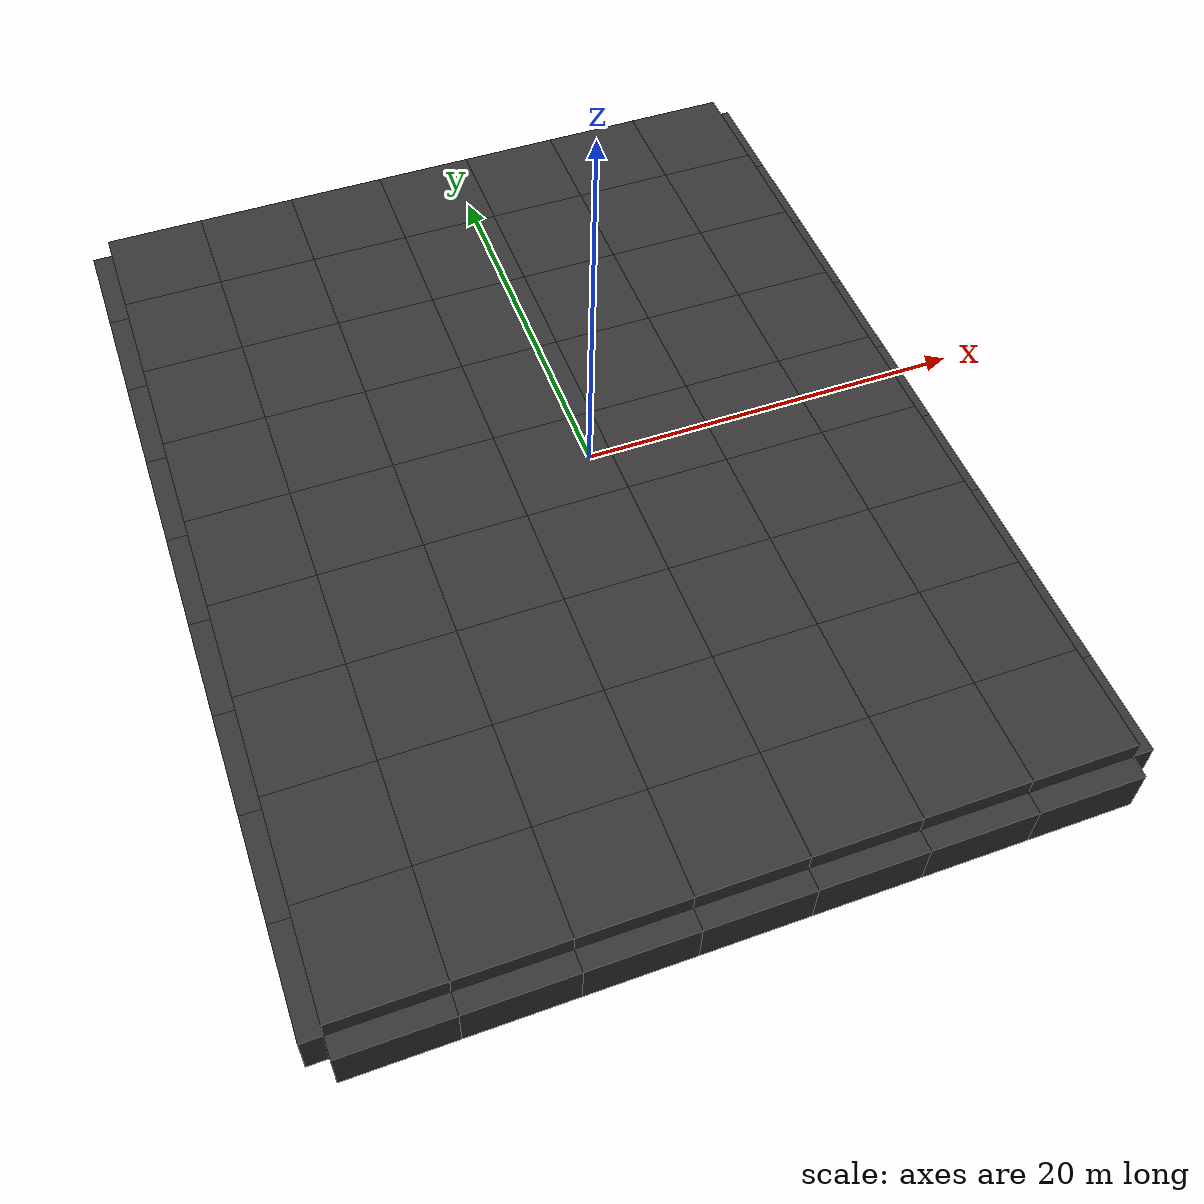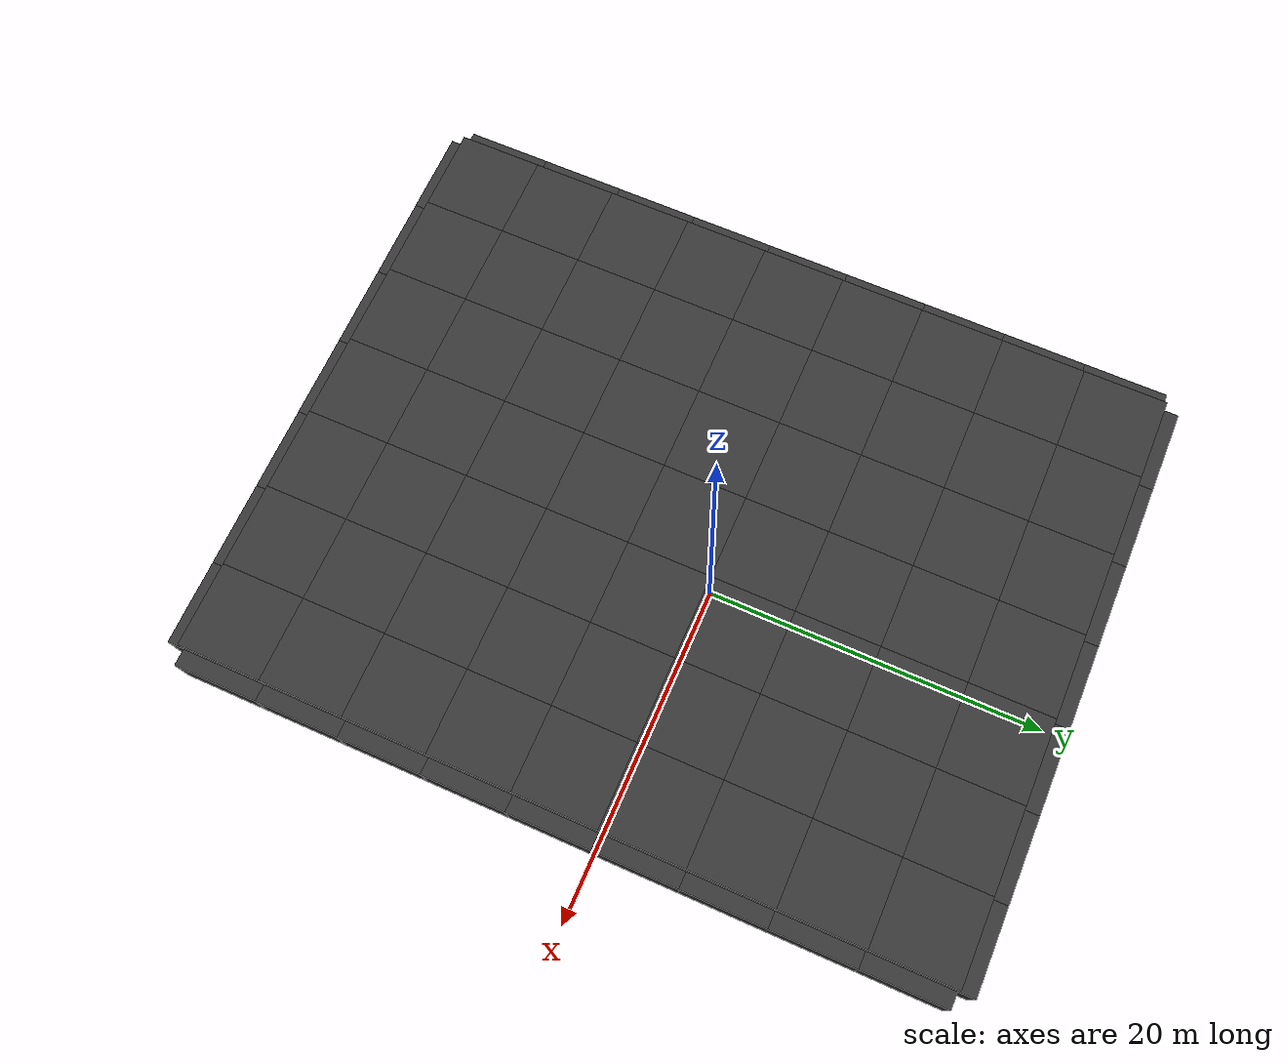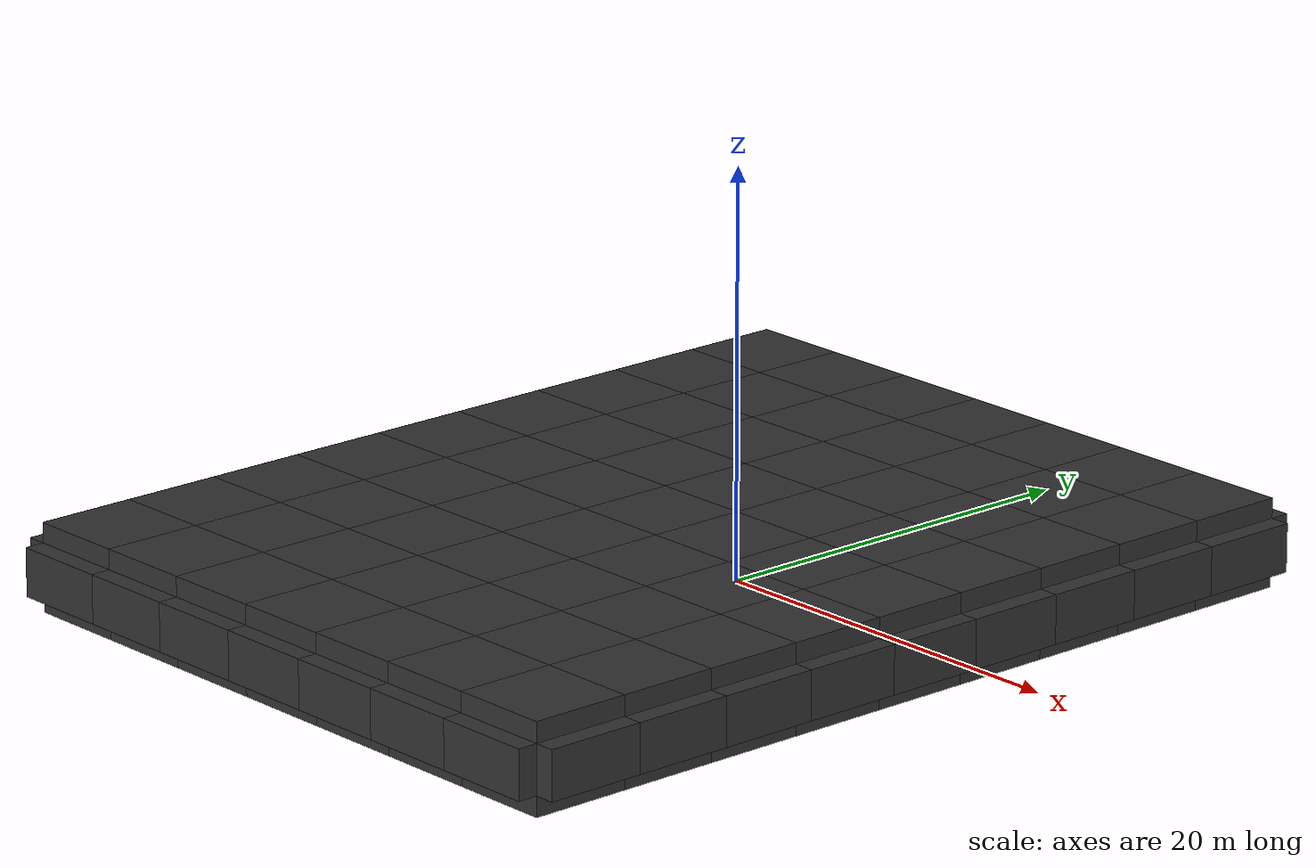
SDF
<sdf version="1.7">
 <world name="RG1">
  <plugin filename="gz-sim-physics-system" name="gz::sim::systems::Physics"/>
  <plugin filename="gz-sim-sensors-system" name="gz::sim::systems::Sensors">
   <render_engine>ogre2</render_engine>
  </plugin>
  <plugin filename="gz-sim-scene-broadcaster-system" name="gz::sim::systems::SceneBroadcaster"/>
  <plugin filename="gz-sim-user-commands-system" name="gz::sim::systems::UserCommands"/>
  <physics name="fast" type="ignored">
   <max_step_size>0.004</max_step_size>
   <real_time_factor>1</real_time_factor>
  </physics>
  <model name="floor_1">
   <static>true</static>
   <pose>-17.5 -22.5 -0.5 0.0 0.0 0.0</pose>
   <link name="floor_1-base-link">
    <visual name="floor_1-visual">
     <geometry><box><size>5 5 1.0</size></box></geometry>
     <material><diffuse>0.2 0.2 0.2 1</diffuse><specular>0.1 0.1 0.1 1</specular></material>
    </visual>
    <collision name="floor_1-collision"><geometry><box><size>5 5 1.0</size></box></geometry></collision>
   </link>
  </model>
  <model name="ceiling_1">
   <static>true</static>
   <pose>-17.5 -22.5 2.9 0.0 0.0 0.0</pose>
   <link name="ceiling_1-base-link">
    <visual name="ceiling_1-visual">
     <geometry><box><size>5 5 1.0</size></box></geometry>
     <material><diffuse>0.2 0.2 0.2 1</diffuse><specular>0.1 0.1 0.1 1</specular></material>
    </visual>
    <collision name="ceiling_1-collision"><geometry><box><size>5 5 1.0</size></box></geometry></collision>
    <light type="point" name="ceiling_1-light">
     <pose>0 0 -1 0 0 0</pose>
     <cast_shadows>false</cast_shadows>
     <diffuse>0.8 0.8 0.8 1</diffuse>
     <attenuation>
      <range>10</range>
      <constant>0.8</constant>
      <linear>0.05</linear>
      <quadratic>0.01</quadratic>
     </attenuation>
    </light>
   </link>
  </model>
  <model name="wall_1">
   <static>true</static>
   <pose>-20.5 -22.5 1.2 0.0 0.0 1.570796326795</pose>
   <link name="wall_1-base-link">
    <visual name="wall_1-visual">
     <geometry><box><size>5 1 2.4</size></box></geometry>
     <material><diffuse>0.2 0.2 0.2 1</diffuse><specular>0.1 0.1 0.1 1</specular></material>
    </visual>
    <collision name="wall_1-collision"><geometry><box><size>5 1 2.4</size></box></geometry></collision>
   </link>
  </model>
  <model name="wall_2">
   <static>true</static>
   <pose>-17.5 -25.5 1.2 0.0 0.0 0.0</pose>
   <link name="wall_2-base-link">
    <visual name="wall_2-visual">
     <geometry><box><size>5 1 2.4</size></box></geometry>
     <material><diffuse>0.2 0.2 0.2 1</diffuse><specular>0.1 0.1 0.1 1</specular></material>
    </visual>
    <collision name="wall_2-collision"><geometry><box><size>5 1 2.4</size></box></geometry></collision>
   </link>
  </model>
  <model name="floor_2">
   <static>true</static>
   <pose>-17.5 -17.5 -0.5 0.0 0.0 0.0</pose>
   <link name="floor_2-base-link">
    <visual name="floor_2-visual">
     <geometry><box><size>5 5 1.0</size></box></geometry>
     <material><diffuse>0.2 0.2 0.2 1</diffuse><specular>0.1 0.1 0.1 1</specular></material>
    </visual>
    <collision name="floor_2-collision"><geometry><box><size>5 5 1.0</size></box></geometry></collision>
   </link>
  </model>
  <model name="ceiling_2">
   <static>true</static>
   <pose>-17.5 -17.5 2.9 0.0 0.0 0.0</pose>
   <link name="ceiling_2-base-link">
    <visual name="ceiling_2-visual">
     <geometry><box><size>5 5 1.0</size></box></geometry>
     <material><diffuse>0.2 0.2 0.2 1</diffuse><specular>0.1 0.1 0.1 1</specular></material>
    </visual>
    <collision name="ceiling_2-collision"><geometry><box><size>5 5 1.0</size></box></geometry></collision>
    <light type="point" name="ceiling_2-light">
     <pose>0 0 -1 0 0 0</pose>
     <cast_shadows>false</cast_shadows>
     <diffuse>0.8 0.8 0.8 1</diffuse>
     <attenuation>
      <range>10</range>
      <constant>0.8</constant>
      <linear>0.05</linear>
      <quadratic>0.01</quadratic>
     </attenuation>
    </light>
   </link>
  </model>
  <model name="wall_3">
   <static>true</static>
   <pose>-20.5 -17.5 1.2 0.0 0.0 1.570796326795</pose>
   <link name="wall_3-base-link">
    <visual name="wall_3-visual">
     <geometry><box><size>5 1 2.4</size></box></geometry>
     <material><diffuse>0.2 0.2 0.2 1</diffuse><specular>0.1 0.1 0.1 1</specular></material>
    </visual>
    <collision name="wall_3-collision"><geometry><box><size>5 1 2.4</size></box></geometry></collision>
   </link>
  </model>
  <model name="floor_3">
   <static>true</static>
   <pose>-17.5 -12.5 -0.5 0.0 0.0 0.0</pose>
   <link name="floor_3-base-link">
    <visual name="floor_3-visual">
     <geometry><box><size>5 5 1.0</size></box></geometry>
     <material><diffuse>0.2 0.2 0.2 1</diffuse><specular>0.1 0.1 0.1 1</specular></material>
    </visual>
    <collision name="floor_3-collision"><geometry><box><size>5 5 1.0</size></box></geometry></collision>
   </link>
  </model>
  <model name="ceiling_3">
   <static>true</static>
   <pose>-17.5 -12.5 2.9 0.0 0.0 0.0</pose>
   <link name="ceiling_3-base-link">
    <visual name="ceiling_3-visual">
     <geometry><box><size>5 5 1.0</size></box></geometry>
     <material><diffuse>0.2 0.2 0.2 1</diffuse><specular>0.1 0.1 0.1 1</specular></material>
    </visual>
    <collision name="ceiling_3-collision"><geometry><box><size>5 5 1.0</size></box></geometry></collision>
    <light type="point" name="ceiling_3-light">
     <pose>0 0 -1 0 0 0</pose>
     <cast_shadows>false</cast_shadows>
     <diffuse>0.8 0.8 0.8 1</diffuse>
     <attenuation>
      <range>10</range>
      <constant>0.8</constant>
      <linear>0.05</linear>
      <quadratic>0.01</quadratic>
     </attenuation>
    </light>
   </link>
  </model>
  <model name="wall_4">
   <static>true</static>
   <pose>-20.5 -12.5 1.2 0.0 0.0 1.570796326795</pose>
   <link name="wall_4-base-link">
    <visual name="wall_4-visual">
     <geometry><box><size>5 1 2.4</size></box></geometry>
     <material><diffuse>0.2 0.2 0.2 1</diffuse><specular>0.1 0.1 0.1 1</specular></material>
    </visual>
    <collision name="wall_4-collision"><geometry><box><size>5 1 2.4</size></box></geometry></collision>
   </link>
  </model>
  <model name="floor_4">
   <static>true</static>
   <pose>-17.5 -7.5 -0.5 0.0 0.0 0.0</pose>
   <link name="floor_4-base-link">
    <visual name="floor_4-visual">
     <geometry><box><size>5 5 1.0</size></box></geometry>
     <material><diffuse>0.2 0.2 0.2 1</diffuse><specular>0.1 0.1 0.1 1</specular></material>
    </visual>
    <collision name="floor_4-collision"><geometry><box><size>5 5 1.0</size></box></geometry></collision>
   </link>
  </model>
  <model name="ceiling_4">
   <static>true</static>
   <pose>-17.5 -7.5 2.9 0.0 0.0 0.0</pose>
   <link name="ceiling_4-base-link">
    <visual name="ceiling_4-visual">
     <geometry><box><size>5 5 1.0</size></box></geometry>
     <material><diffuse>0.2 0.2 0.2 1</diffuse><specular>0.1 0.1 0.1 1</specular></material>
    </visual>
    <collision name="ceiling_4-collision"><geometry><box><size>5 5 1.0</size></box></geometry></collision>
    <light type="point" name="ceiling_4-light">
     <pose>0 0 -1 0 0 0</pose>
     <cast_shadows>false</cast_shadows>
     <diffuse>0.8 0.8 0.8 1</diffuse>
     <attenuation>
      <range>10</range>
      <constant>0.8</constant>
      <linear>0.05</linear>
      <quadratic>0.01</quadratic>
     </attenuation>
    </light>
   </link>
  </model>
  <model name="wall_5">
   <static>true</static>
   <pose>-20.5 -7.5 1.2 0.0 0.0 1.570796326795</pose>
   <link name="wall_5-base-link">
    <visual name="wall_5-visual">
     <geometry><box><size>5 1 2.4</size></box></geometry>
     <material><diffuse>0.2 0.2 0.2 1</diffuse><specular>0.1 0.1 0.1 1</specular></material>
    </visual>
    <collision name="wall_5-collision"><geometry><box><size>5 1 2.4</size></box></geometry></collision>
   </link>
  </model>
  <model name="floor_5">
   <static>true</static>
   <pose>-17.5 -2.5 -0.5 0.0 0.0 0.0</pose>
   <link name="floor_5-base-link">
    <visual name="floor_5-visual">
     <geometry><box><size>5 5 1.0</size></box></geometry>
     <material><diffuse>0.2 0.2 0.2 1</diffuse><specular>0.1 0.1 0.1 1</specular></material>
    </visual>
    <collision name="floor_5-collision"><geometry><box><size>5 5 1.0</size></box></geometry></collision>
   </link>
  </model>
  <model name="ceiling_5">
   <static>true</static>
   <pose>-17.5 -2.5 2.9 0.0 0.0 0.0</pose>
   <link name="ceiling_5-base-link">
    <visual name="ceiling_5-visual">
     <geometry><box><size>5 5 1.0</size></box></geometry>
     <material><diffuse>0.2 0.2 0.2 1</diffuse><specular>0.1 0.1 0.1 1</specular></material>
    </visual>
    <collision name="ceiling_5-collision"><geometry><box><size>5 5 1.0</size></box></geometry></collision>
    <light type="point" name="ceiling_5-light">
     <pose>0 0 -1 0 0 0</pose>
     <cast_shadows>false</cast_shadows>
     <diffuse>0.8 0.8 0.8 1</diffuse>
     <attenuation>
      <range>10</range>
      <constant>0.8</constant>
      <linear>0.05</linear>
      <quadratic>0.01</quadratic>
     </attenuation>
    </light>
   </link>
  </model>
  <model name="wall_6">
   <static>true</static>
   <pose>-20.5 -2.5 1.2 0.0 0.0 1.570796326795</pose>
   <link name="wall_6-base-link">
    <visual name="wall_6-visual">
     <geometry><box><size>5 1 2.4</size></box></geometry>
     <material><diffuse>0.2 0.2 0.2 1</diffuse><specular>0.1 0.1 0.1 1</specular></material>
    </visual>
    <collision name="wall_6-collision"><geometry><box><size>5 1 2.4</size></box></geometry></collision>
   </link>
  </model>
  <model name="floor_6">
   <static>true</static>
   <pose>-17.5 2.5 -0.5 0.0 0.0 0.0</pose>
   <link name="floor_6-base-link">
    <visual name="floor_6-visual">
     <geometry><box><size>5 5 1.0</size></box></geometry>
     <material><diffuse>0.2 0.2 0.2 1</diffuse><specular>0.1 0.1 0.1 1</specular></material>
    </visual>
    <collision name="floor_6-collision"><geometry><box><size>5 5 1.0</size></box></geometry></collision>
   </link>
  </model>
  <model name="ceiling_6">
   <static>true</static>
   <pose>-17.5 2.5 2.9 0.0 0.0 0.0</pose>
   <link name="ceiling_6-base-link">
    <visual name="ceiling_6-visual">
     <geometry><box><size>5 5 1.0</size></box></geometry>
     <material><diffuse>0.2 0.2 0.2 1</diffuse><specular>0.1 0.1 0.1 1</specular></material>
    </visual>
    <collision name="ceiling_6-collision"><geometry><box><size>5 5 1.0</size></box></geometry></collision>
    <light type="point" name="ceiling_6-light">
     <pose>0 0 -1 0 0 0</pose>
     <cast_shadows>false</cast_shadows>
     <diffuse>0.8 0.8 0.8 1</diffuse>
     <attenuation>
      <range>10</range>
      <constant>0.8</constant>
      <linear>0.05</linear>
      <quadratic>0.01</quadratic>
     </attenuation>
    </light>
   </link>
  </model>
  <model name="wall_7">
   <static>true</static>
   <pose>-20.5 2.5 1.2 0.0 0.0 1.570796326795</pose>
   <link name="wall_7-base-link">
    <visual name="wall_7-visual">
     <geometry><box><size>5 1 2.4</size></box></geometry>
     <material><diffuse>0.2 0.2 0.2 1</diffuse><specular>0.1 0.1 0.1 1</specular></material>
    </visual>
    <collision name="wall_7-collision"><geometry><box><size>5 1 2.4</size></box></geometry></collision>
   </link>
  </model>
  <model name="floor_7">
   <static>true</static>
   <pose>-17.5 7.5 -0.5 0.0 0.0 0.0</pose>
   <link name="floor_7-base-link">
    <visual name="floor_7-visual">
     <geometry><box><size>5 5 1.0</size></box></geometry>
     <material><diffuse>0.2 0.2 0.2 1</diffuse><specular>0.1 0.1 0.1 1</specular></material>
    </visual>
    <collision name="floor_7-collision"><geometry><box><size>5 5 1.0</size></box></geometry></collision>
   </link>
  </model>
  <model name="ceiling_7">
   <static>true</static>
   <pose>-17.5 7.5 2.9 0.0 0.0 0.0</pose>
   <link name="ceiling_7-base-link">
    <visual name="ceiling_7-visual">
     <geometry><box><size>5 5 1.0</size></box></geometry>
     <material><diffuse>0.2 0.2 0.2 1</diffuse><specular>0.1 0.1 0.1 1</specular></material>
    </visual>
    <collision name="ceiling_7-collision"><geometry><box><size>5 5 1.0</size></box></geometry></collision>
    <light type="point" name="ceiling_7-light">
     <pose>0 0 -1 0 0 0</pose>
     <cast_shadows>false</cast_shadows>
     <diffuse>0.8 0.8 0.8 1</diffuse>
     <attenuation>
      <range>10</range>
      <constant>0.8</constant>
      <linear>0.05</linear>
      <quadratic>0.01</quadratic>
     </attenuation>
    </light>
   </link>
  </model>
  <model name="wall_8">
   <static>true</static>
   <pose>-20.5 7.5 1.2 0.0 0.0 1.570796326795</pose>
   <link name="wall_8-base-link">
    <visual name="wall_8-visual">
     <geometry><box><size>5 1 2.4</size></box></geometry>
     <material><diffuse>0.2 0.2 0.2 1</diffuse><specular>0.1 0.1 0.1 1</specular></material>
    </visual>
    <collision name="wall_8-collision"><geometry><box><size>5 1 2.4</size></box></geometry></collision>
   </link>
  </model>
  <model name="floor_8">
   <static>true</static>
   <pose>-17.5 12.5 -0.5 0.0 0.0 0.0</pose>
   <link name="floor_8-base-link">
    <visual name="floor_8-visual">
     <geometry><box><size>5 5 1.0</size></box></geometry>
     <material><diffuse>0.2 0.2 0.2 1</diffuse><specular>0.1 0.1 0.1 1</specular></material>
    </visual>
    <collision name="floor_8-collision"><geometry><box><size>5 5 1.0</size></box></geometry></collision>
   </link>
  </model>
  <model name="ceiling_8">
   <static>true</static>
   <pose>-17.5 12.5 2.9 0.0 0.0 0.0</pose>
   <link name="ceiling_8-base-link">
    <visual name="ceiling_8-visual">
     <geometry><box><size>5 5 1.0</size></box></geometry>
     <material><diffuse>0.2 0.2 0.2 1</diffuse><specular>0.1 0.1 0.1 1</specular></material>
    </visual>
    <collision name="ceiling_8-collision"><geometry><box><size>5 5 1.0</size></box></geometry></collision>
    <light type="point" name="ceiling_8-light">
     <pose>0 0 -1 0 0 0</pose>
     <cast_shadows>false</cast_shadows>
     <diffuse>0.8 0.8 0.8 1</diffuse>
     <attenuation>
      <range>10</range>
      <constant>0.8</constant>
      <linear>0.05</linear>
      <quadratic>0.01</quadratic>
     </attenuation>
    </light>
   </link>
  </model>
  <model name="wall_9">
   <static>true</static>
   <pose>-20.5 12.5 1.2 0.0 0.0 1.570796326795</pose>
   <link name="wall_9-base-link">
    <visual name="wall_9-visual">
     <geometry><box><size>5 1 2.4</size></box></geometry>
     <material><diffuse>0.2 0.2 0.2 1</diffuse><specular>0.1 0.1 0.1 1</specular></material>
    </visual>
    <collision name="wall_9-collision"><geometry><box><size>5 1 2.4</size></box></geometry></collision>
   </link>
  </model>
  <model name="floor_9">
   <static>true</static>
   <pose>-17.5 17.5 -0.5 0.0 0.0 0.0</pose>
   <link name="floor_9-base-link">
    <visual name="floor_9-visual">
     <geometry><box><size>5 5 1.0</size></box></geometry>
     <material><diffuse>0.2 0.2 0.2 1</diffuse><specular>0.1 0.1 0.1 1</specular></material>
    </visual>
    <collision name="floor_9-collision"><geometry><box><size>5 5 1.0</size></box></geometry></collision>
   </link>
  </model>
  <model name="ceiling_9">
   <static>true</static>
   <pose>-17.5 17.5 2.9 0.0 0.0 0.0</pose>
   <link name="ceiling_9-base-link">
    <visual name="ceiling_9-visual">
     <geometry><box><size>5 5 1.0</size></box></geometry>
     <material><diffuse>0.2 0.2 0.2 1</diffuse><specular>0.1 0.1 0.1 1</specular></material>
    </visual>
    <collision name="ceiling_9-collision"><geometry><box><size>5 5 1.0</size></box></geometry></collision>
    <light type="point" name="ceiling_9-light">
     <pose>0 0 -1 0 0 0</pose>
     <cast_shadows>false</cast_shadows>
     <diffuse>0.8 0.8 0.8 1</diffuse>
     <attenuation>
      <range>10</range>
      <constant>0.8</constant>
      <linear>0.05</linear>
      <quadratic>0.01</quadratic>
     </attenuation>
    </light>
   </link>
  </model>
  <model name="wall_10">
   <static>true</static>
   <pose>-20.5 17.5 1.2 0.0 0.0 1.570796326795</pose>
   <link name="wall_10-base-link">
    <visual name="wall_10-visual">
     <geometry><box><size>5 1 2.4</size></box></geometry>
     <material><diffuse>0.2 0.2 0.2 1</diffuse><specular>0.1 0.1 0.1 1</specular></material>
    </visual>
    <collision name="wall_10-collision"><geometry><box><size>5 1 2.4</size></box></geometry></collision>
   </link>
  </model>
  <model name="wall_11">
   <static>true</static>
   <pose>-17.5 20.5 1.2 0.0 0.0 0.0</pose>
   <link name="wall_11-base-link">
    <visual name="wall_11-visual">
     <geometry><box><size>5 1 2.4</size></box></geometry>
     <material><diffuse>0.2 0.2 0.2 1</diffuse><specular>0.1 0.1 0.1 1</specular></material>
    </visual>
    <collision name="wall_11-collision"><geometry><box><size>5 1 2.4</size></box></geometry></collision>
   </link>
  </model>
  <model name="floor_10">
   <static>true</static>
   <pose>-12.5 -22.5 -0.5 0.0 0.0 0.0</pose>
   <link name="floor_10-base-link">
    <visual name="floor_10-visual">
     <geometry><box><size>5 5 1.0</size></box></geometry>
     <material><diffuse>0.2 0.2 0.2 1</diffuse><specular>0.1 0.1 0.1 1</specular></material>
    </visual>
    <collision name="floor_10-collision"><geometry><box><size>5 5 1.0</size></box></geometry></collision>
   </link>
  </model>
  <model name="ceiling_10">
   <static>true</static>
   <pose>-12.5 -22.5 2.9 0.0 0.0 0.0</pose>
   <link name="ceiling_10-base-link">
    <visual name="ceiling_10-visual">
     <geometry><box><size>5 5 1.0</size></box></geometry>
     <material><diffuse>0.2 0.2 0.2 1</diffuse><specular>0.1 0.1 0.1 1</specular></material>
    </visual>
    <collision name="ceiling_10-collision"><geometry><box><size>5 5 1.0</size></box></geometry></collision>
    <light type="point" name="ceiling_10-light">
     <pose>0 0 -1 0 0 0</pose>
     <cast_shadows>false</cast_shadows>
     <diffuse>0.8 0.8 0.8 1</diffuse>
     <attenuation>
      <range>10</range>
      <constant>0.8</constant>
      <linear>0.05</linear>
      <quadratic>0.01</quadratic>
     </attenuation>
    </light>
   </link>
  </model>
  <model name="wall_12">
   <static>true</static>
   <pose>-12.5 -25.5 1.2 0.0 0.0 0.0</pose>
   <link name="wall_12-base-link">
    <visual name="wall_12-visual">
     <geometry><box><size>5 1 2.4</size></box></geometry>
     <material><diffuse>0.2 0.2 0.2 1</diffuse><specular>0.1 0.1 0.1 1</specular></material>
    </visual>
    <collision name="wall_12-collision"><geometry><box><size>5 1 2.4</size></box></geometry></collision>
   </link>
  </model>
  <model name="floor_11">
   <static>true</static>
   <pose>-12.5 -17.5 -0.5 0.0 0.0 0.0</pose>
   <link name="floor_11-base-link">
    <visual name="floor_11-visual">
     <geometry><box><size>5 5 1.0</size></box></geometry>
     <material><diffuse>0.2 0.2 0.2 1</diffuse><specular>0.1 0.1 0.1 1</specular></material>
    </visual>
    <collision name="floor_11-collision"><geometry><box><size>5 5 1.0</size></box></geometry></collision>
   </link>
  </model>
  <model name="ceiling_11">
   <static>true</static>
   <pose>-12.5 -17.5 2.9 0.0 0.0 0.0</pose>
   <link name="ceiling_11-base-link">
    <visual name="ceiling_11-visual">
     <geometry><box><size>5 5 1.0</size></box></geometry>
     <material><diffuse>0.2 0.2 0.2 1</diffuse><specular>0.1 0.1 0.1 1</specular></material>
    </visual>
    <collision name="ceiling_11-collision"><geometry><box><size>5 5 1.0</size></box></geometry></collision>
    <light type="point" name="ceiling_11-light">
     <pose>0 0 -1 0 0 0</pose>
     <cast_shadows>false</cast_shadows>
     <diffuse>0.8 0.8 0.8 1</diffuse>
     <attenuation>
      <range>10</range>
      <constant>0.8</constant>
      <linear>0.05</linear>
      <quadratic>0.01</quadratic>
     </attenuation>
    </light>
   </link>
  </model>
  <model name="floor_12">
   <static>true</static>
   <pose>-12.5 -12.5 -0.5 0.0 0.0 0.0</pose>
   <link name="floor_12-base-link">
    <visual name="floor_12-visual">
     <geometry><box><size>5 5 1.0</size></box></geometry>
     <material><diffuse>0.2 0.2 0.2 1</diffuse><specular>0.1 0.1 0.1 1</specular></material>
    </visual>
    <collision name="floor_12-collision"><geometry><box><size>5 5 1.0</size></box></geometry></collision>
   </link>
  </model>
  <model name="ceiling_12">
   <static>true</static>
   <pose>-12.5 -12.5 2.9 0.0 0.0 0.0</pose>
   <link name="ceiling_12-base-link">
    <visual name="ceiling_12-visual">
     <geometry><box><size>5 5 1.0</size></box></geometry>
     <material><diffuse>0.2 0.2 0.2 1</diffuse><specular>0.1 0.1 0.1 1</specular></material>
    </visual>
    <collision name="ceiling_12-collision"><geometry><box><size>5 5 1.0</size></box></geometry></collision>
    <light type="point" name="ceiling_12-light">
     <pose>0 0 -1 0 0 0</pose>
     <cast_shadows>false</cast_shadows>
     <diffuse>0.8 0.8 0.8 1</diffuse>
     <attenuation>
      <range>10</range>
      <constant>0.8</constant>
      <linear>0.05</linear>
      <quadratic>0.01</quadratic>
     </attenuation>
    </light>
   </link>
  </model>
  <model name="floor_13">
   <static>true</static>
   <pose>-12.5 -7.5 -0.5 0.0 0.0 0.0</pose>
   <link name="floor_13-base-link">
    <visual name="floor_13-visual">
     <geometry><box><size>5 5 1.0</size></box></geometry>
     <material><diffuse>0.2 0.2 0.2 1</diffuse><specular>0.1 0.1 0.1 1</specular></material>
    </visual>
    <collision name="floor_13-collision"><geometry><box><size>5 5 1.0</size></box></geometry></collision>
   </link>
  </model>
  <model name="ceiling_13">
   <static>true</static>
   <pose>-12.5 -7.5 2.9 0.0 0.0 0.0</pose>
   <link name="ceiling_13-base-link">
    <visual name="ceiling_13-visual">
     <geometry><box><size>5 5 1.0</size></box></geometry>
     <material><diffuse>0.2 0.2 0.2 1</diffuse><specular>0.1 0.1 0.1 1</specular></material>
    </visual>
    <collision name="ceiling_13-collision"><geometry><box><size>5 5 1.0</size></box></geometry></collision>
    <light type="point" name="ceiling_13-light">
     <pose>0 0 -1 0 0 0</pose>
     <cast_shadows>false</cast_shadows>
     <diffuse>0.8 0.8 0.8 1</diffuse>
     <attenuation>
      <range>10</range>
      <constant>0.8</constant>
      <linear>0.05</linear>
      <quadratic>0.01</quadratic>
     </attenuation>
    </light>
   </link>
  </model>
  <model name="floor_14">
   <static>true</static>
   <pose>-12.5 -2.5 -0.5 0.0 0.0 0.0</pose>
   <link name="floor_14-base-link">
    <visual name="floor_14-visual">
     <geometry><box><size>5 5 1.0</size></box></geometry>
     <material><diffuse>0.2 0.2 0.2 1</diffuse><specular>0.1 0.1 0.1 1</specular></material>
    </visual>
    <collision name="floor_14-collision"><geometry><box><size>5 5 1.0</size></box></geometry></collision>
   </link>
  </model>
  <model name="ceiling_14">
   <static>true</static>
   <pose>-12.5 -2.5 2.9 0.0 0.0 0.0</pose>
   <link name="ceiling_14-base-link">
    <visual name="ceiling_14-visual">
     <geometry><box><size>5 5 1.0</size></box></geometry>
     <material><diffuse>0.2 0.2 0.2 1</diffuse><specular>0.1 0.1 0.1 1</specular></material>
    </visual>
    <collision name="ceiling_14-collision"><geometry><box><size>5 5 1.0</size></box></geometry></collision>
    <light type="point" name="ceiling_14-light">
     <pose>0 0 -1 0 0 0</pose>
     <cast_shadows>false</cast_shadows>
     <diffuse>0.8 0.8 0.8 1</diffuse>
     <attenuation>
      <range>10</range>
      <constant>0.8</constant>
      <linear>0.05</linear>
      <quadratic>0.01</quadratic>
     </attenuation>
    </light>
   </link>
  </model>
  <model name="floor_15">
   <static>true</static>
   <pose>-12.5 2.5 -0.5 0.0 0.0 0.0</pose>
   <link name="floor_15-base-link">
    <visual name="floor_15-visual">
     <geometry><box><size>5 5 1.0</size></box></geometry>
     <material><diffuse>0.2 0.2 0.2 1</diffuse><specular>0.1 0.1 0.1 1</specular></material>
    </visual>
    <collision name="floor_15-collision"><geometry><box><size>5 5 1.0</size></box></geometry></collision>
   </link>
  </model>
  <model name="ceiling_15">
   <static>true</static>
   <pose>-12.5 2.5 2.9 0.0 0.0 0.0</pose>
   <link name="ceiling_15-base-link">
    <visual name="ceiling_15-visual">
     <geometry><box><size>5 5 1.0</size></box></geometry>
     <material><diffuse>0.2 0.2 0.2 1</diffuse><specular>0.1 0.1 0.1 1</specular></material>
    </visual>
    <collision name="ceiling_15-collision"><geometry><box><size>5 5 1.0</size></box></geometry></collision>
    <light type="point" name="ceiling_15-light">
     <pose>0 0 -1 0 0 0</pose>
     <cast_shadows>false</cast_shadows>
     <diffuse>0.8 0.8 0.8 1</diffuse>
     <attenuation>
      <range>10</range>
      <constant>0.8</constant>
      <linear>0.05</linear>
      <quadratic>0.01</quadratic>
     </attenuation>
    </light>
   </link>
  </model>
  <model name="floor_16">
   <static>true</static>
   <pose>-12.5 7.5 -0.5 0.0 0.0 0.0</pose>
   <link name="floor_16-base-link">
    <visual name="floor_16-visual">
     <geometry><box><size>5 5 1.0</size></box></geometry>
     <material><diffuse>0.2 0.2 0.2 1</diffuse><specular>0.1 0.1 0.1 1</specular></material>
    </visual>
    <collision name="floor_16-collision"><geometry><box><size>5 5 1.0</size></box></geometry></collision>
   </link>
  </model>
  <model name="ceiling_16">
   <static>true</static>
   <pose>-12.5 7.5 2.9 0.0 0.0 0.0</pose>
   <link name="ceiling_16-base-link">
    <visual name="ceiling_16-visual">
     <geometry><box><size>5 5 1.0</size></box></geometry>
     <material><diffuse>0.2 0.2 0.2 1</diffuse><specular>0.1 0.1 0.1 1</specular></material>
    </visual>
    <collision name="ceiling_16-collision"><geometry><box><size>5 5 1.0</size></box></geometry></collision>
    <light type="point" name="ceiling_16-light">
     <pose>0 0 -1 0 0 0</pose>
     <cast_shadows>false</cast_shadows>
     <diffuse>0.8 0.8 0.8 1</diffuse>
     <attenuation>
      <range>10</range>
      <constant>0.8</constant>
      <linear>0.05</linear>
      <quadratic>0.01</quadratic>
     </attenuation>
    </light>
   </link>
  </model>
  <model name="floor_17">
   <static>true</static>
   <pose>-12.5 12.5 -0.5 0.0 0.0 0.0</pose>
   <link name="floor_17-base-link">
    <visual name="floor_17-visual">
     <geometry><box><size>5 5 1.0</size></box></geometry>
     <material><diffuse>0.2 0.2 0.2 1</diffuse><specular>0.1 0.1 0.1 1</specular></material>
    </visual>
    <collision name="floor_17-collision"><geometry><box><size>5 5 1.0</size></box></geometry></collision>
   </link>
  </model>
  <model name="ceiling_17">
   <static>true</static>
   <pose>-12.5 12.5 2.9 0.0 0.0 0.0</pose>
   <link name="ceiling_17-base-link">
    <visual name="ceiling_17-visual">
     <geometry><box><size>5 5 1.0</size></box></geometry>
     <material><diffuse>0.2 0.2 0.2 1</diffuse><specular>0.1 0.1 0.1 1</specular></material>
    </visual>
    <collision name="ceiling_17-collision"><geometry><box><size>5 5 1.0</size></box></geometry></collision>
    <light type="point" name="ceiling_17-light">
     <pose>0 0 -1 0 0 0</pose>
     <cast_shadows>false</cast_shadows>
     <diffuse>0.8 0.8 0.8 1</diffuse>
     <attenuation>
      <range>10</range>
      <constant>0.8</constant>
      <linear>0.05</linear>
      <quadratic>0.01</quadratic>
     </attenuation>
    </light>
   </link>
  </model>
  <model name="floor_18">
   <static>true</static>
   <pose>-12.5 17.5 -0.5 0.0 0.0 0.0</pose>
   <link name="floor_18-base-link">
    <visual name="floor_18-visual">
     <geometry><box><size>5 5 1.0</size></box></geometry>
     <material><diffuse>0.2 0.2 0.2 1</diffuse><specular>0.1 0.1 0.1 1</specular></material>
    </visual>
    <collision name="floor_18-collision"><geometry><box><size>5 5 1.0</size></box></geometry></collision>
   </link>
  </model>
  <model name="ceiling_18">
   <static>true</static>
   <pose>-12.5 17.5 2.9 0.0 0.0 0.0</pose>
   <link name="ceiling_18-base-link">
    <visual name="ceiling_18-visual">
     <geometry><box><size>5 5 1.0</size></box></geometry>
     <material><diffuse>0.2 0.2 0.2 1</diffuse><specular>0.1 0.1 0.1 1</specular></material>
    </visual>
    <collision name="ceiling_18-collision"><geometry><box><size>5 5 1.0</size></box></geometry></collision>
    <light type="point" name="ceiling_18-light">
     <pose>0 0 -1 0 0 0</pose>
     <cast_shadows>false</cast_shadows>
     <diffuse>0.8 0.8 0.8 1</diffuse>
     <attenuation>
      <range>10</range>
      <constant>0.8</constant>
      <linear>0.05</linear>
      <quadratic>0.01</quadratic>
     </attenuation>
    </light>
   </link>
  </model>
  <model name="wall_13">
   <static>true</static>
   <pose>-12.5 20.5 1.2 0.0 0.0 0.0</pose>
   <link name="wall_13-base-link">
    <visual name="wall_13-visual">
     <geometry><box><size>5 1 2.4</size></box></geometry>
     <material><diffuse>0.2 0.2 0.2 1</diffuse><specular>0.1 0.1 0.1 1</specular></material>
    </visual>
    <collision name="wall_13-collision"><geometry><box><size>5 1 2.4</size></box></geometry></collision>
   </link>
  </model>
  <model name="floor_19">
   <static>true</static>
   <pose>-7.5 -22.5 -0.5 0.0 0.0 0.0</pose>
   <link name="floor_19-base-link">
    <visual name="floor_19-visual">
     <geometry><box><size>5 5 1.0</size></box></geometry>
     <material><diffuse>0.2 0.2 0.2 1</diffuse><specular>0.1 0.1 0.1 1</specular></material>
    </visual>
    <collision name="floor_19-collision"><geometry><box><size>5 5 1.0</size></box></geometry></collision>
   </link>
  </model>
  <model name="ceiling_19">
   <static>true</static>
   <pose>-7.5 -22.5 2.9 0.0 0.0 0.0</pose>
   <link name="ceiling_19-base-link">
    <visual name="ceiling_19-visual">
     <geometry><box><size>5 5 1.0</size></box></geometry>
     <material><diffuse>0.2 0.2 0.2 1</diffuse><specular>0.1 0.1 0.1 1</specular></material>
    </visual>
    <collision name="ceiling_19-collision"><geometry><box><size>5 5 1.0</size></box></geometry></collision>
    <light type="point" name="ceiling_19-light">
     <pose>0 0 -1 0 0 0</pose>
     <cast_shadows>false</cast_shadows>
     <diffuse>0.8 0.8 0.8 1</diffuse>
     <attenuation>
      <range>10</range>
      <constant>0.8</constant>
      <linear>0.05</linear>
      <quadratic>0.01</quadratic>
     </attenuation>
    </light>
   </link>
  </model>
  <model name="wall_14">
   <static>true</static>
   <pose>-7.5 -25.5 1.2 0.0 0.0 0.0</pose>
   <link name="wall_14-base-link">
    <visual name="wall_14-visual">
     <geometry><box><size>5 1 2.4</size></box></geometry>
     <material><diffuse>0.2 0.2 0.2 1</diffuse><specular>0.1 0.1 0.1 1</specular></material>
    </visual>
    <collision name="wall_14-collision"><geometry><box><size>5 1 2.4</size></box></geometry></collision>
   </link>
  </model>
  <model name="floor_20">
   <static>true</static>
   <pose>-7.5 -17.5 -0.5 0.0 0.0 0.0</pose>
   <link name="floor_20-base-link">
    <visual name="floor_20-visual">
     <geometry><box><size>5 5 1.0</size></box></geometry>
     <material><diffuse>0.2 0.2 0.2 1</diffuse><specular>0.1 0.1 0.1 1</specular></material>
    </visual>
    <collision name="floor_20-collision"><geometry><box><size>5 5 1.0</size></box></geometry></collision>
   </link>
  </model>
  <model name="ceiling_20">
   <static>true</static>
   <pose>-7.5 -17.5 2.9 0.0 0.0 0.0</pose>
   <link name="ceiling_20-base-link">
    <visual name="ceiling_20-visual">
     <geometry><box><size>5 5 1.0</size></box></geometry>
     <material><diffuse>0.2 0.2 0.2 1</diffuse><specular>0.1 0.1 0.1 1</specular></material>
    </visual>
    <collision name="ceiling_20-collision"><geometry><box><size>5 5 1.0</size></box></geometry></collision>
    <light type="point" name="ceiling_20-light">
     <pose>0 0 -1 0 0 0</pose>
     <cast_shadows>false</cast_shadows>
     <diffuse>0.8 0.8 0.8 1</diffuse>
     <attenuation>
      <range>10</range>
      <constant>0.8</constant>
      <linear>0.05</linear>
      <quadratic>0.01</quadratic>
     </attenuation>
    </light>
   </link>
  </model>
  <model name="floor_21">
   <static>true</static>
   <pose>-7.5 -12.5 -0.5 0.0 0.0 0.0</pose>
   <link name="floor_21-base-link">
    <visual name="floor_21-visual">
     <geometry><box><size>5 5 1.0</size></box></geometry>
     <material><diffuse>0.2 0.2 0.2 1</diffuse><specular>0.1 0.1 0.1 1</specular></material>
    </visual>
    <collision name="floor_21-collision"><geometry><box><size>5 5 1.0</size></box></geometry></collision>
   </link>
  </model>
  <model name="ceiling_21">
   <static>true</static>
   <pose>-7.5 -12.5 2.9 0.0 0.0 0.0</pose>
   <link name="ceiling_21-base-link">
    <visual name="ceiling_21-visual">
     <geometry><box><size>5 5 1.0</size></box></geometry>
     <material><diffuse>0.2 0.2 0.2 1</diffuse><specular>0.1 0.1 0.1 1</specular></material>
    </visual>
    <collision name="ceiling_21-collision"><geometry><box><size>5 5 1.0</size></box></geometry></collision>
    <light type="point" name="ceiling_21-light">
     <pose>0 0 -1 0 0 0</pose>
     <cast_shadows>false</cast_shadows>
     <diffuse>0.8 0.8 0.8 1</diffuse>
     <attenuation>
      <range>10</range>
      <constant>0.8</constant>
      <linear>0.05</linear>
      <quadratic>0.01</quadratic>
     </attenuation>
    </light>
   </link>
  </model>
  <model name="floor_22">
   <static>true</static>
   <pose>-7.5 -7.5 -0.5 0.0 0.0 0.0</pose>
   <link name="floor_22-base-link">
    <visual name="floor_22-visual">
     <geometry><box><size>5 5 1.0</size></box></geometry>
     <material><diffuse>0.2 0.2 0.2 1</diffuse><specular>0.1 0.1 0.1 1</specular></material>
    </visual>
    <collision name="floor_22-collision"><geometry><box><size>5 5 1.0</size></box></geometry></collision>
   </link>
  </model>
  <model name="ceiling_22">
   <static>true</static>
   <pose>-7.5 -7.5 2.9 0.0 0.0 0.0</pose>
   <link name="ceiling_22-base-link">
    <visual name="ceiling_22-visual">
     <geometry><box><size>5 5 1.0</size></box></geometry>
     <material><diffuse>0.2 0.2 0.2 1</diffuse><specular>0.1 0.1 0.1 1</specular></material>
    </visual>
    <collision name="ceiling_22-collision"><geometry><box><size>5 5 1.0</size></box></geometry></collision>
    <light type="point" name="ceiling_22-light">
     <pose>0 0 -1 0 0 0</pose>
     <cast_shadows>false</cast_shadows>
     <diffuse>0.8 0.8 0.8 1</diffuse>
     <attenuation>
      <range>10</range>
      <constant>0.8</constant>
      <linear>0.05</linear>
      <quadratic>0.01</quadratic>
     </attenuation>
    </light>
   </link>
  </model>
  <model name="floor_23">
   <static>true</static>
   <pose>-7.5 -2.5 -0.5 0.0 0.0 0.0</pose>
   <link name="floor_23-base-link">
    <visual name="floor_23-visual">
     <geometry><box><size>5 5 1.0</size></box></geometry>
     <material><diffuse>0.2 0.2 0.2 1</diffuse><specular>0.1 0.1 0.1 1</specular></material>
    </visual>
    <collision name="floor_23-collision"><geometry><box><size>5 5 1.0</size></box></geometry></collision>
   </link>
  </model>
  <model name="ceiling_23">
   <static>true</static>
   <pose>-7.5 -2.5 2.9 0.0 0.0 0.0</pose>
   <link name="ceiling_23-base-link">
    <visual name="ceiling_23-visual">
     <geometry><box><size>5 5 1.0</size></box></geometry>
     <material><diffuse>0.2 0.2 0.2 1</diffuse><specular>0.1 0.1 0.1 1</specular></material>
    </visual>
    <collision name="ceiling_23-collision"><geometry><box><size>5 5 1.0</size></box></geometry></collision>
    <light type="point" name="ceiling_23-light">
     <pose>0 0 -1 0 0 0</pose>
     <cast_shadows>false</cast_shadows>
     <diffuse>0.8 0.8 0.8 1</diffuse>
     <attenuation>
      <range>10</range>
      <constant>0.8</constant>
      <linear>0.05</linear>
      <quadratic>0.01</quadratic>
     </attenuation>
    </light>
   </link>
  </model>
  <model name="floor_24">
   <static>true</static>
   <pose>-7.5 2.5 -0.5 0.0 0.0 0.0</pose>
   <link name="floor_24-base-link">
    <visual name="floor_24-visual">
     <geometry><box><size>5 5 1.0</size></box></geometry>
     <material><diffuse>0.2 0.2 0.2 1</diffuse><specular>0.1 0.1 0.1 1</specular></material>
    </visual>
    <collision name="floor_24-collision"><geometry><box><size>5 5 1.0</size></box></geometry></collision>
   </link>
  </model>
  <model name="ceiling_24">
   <static>true</static>
   <pose>-7.5 2.5 2.9 0.0 0.0 0.0</pose>
   <link name="ceiling_24-base-link">
    <visual name="ceiling_24-visual">
     <geometry><box><size>5 5 1.0</size></box></geometry>
     <material><diffuse>0.2 0.2 0.2 1</diffuse><specular>0.1 0.1 0.1 1</specular></material>
    </visual>
    <collision name="ceiling_24-collision"><geometry><box><size>5 5 1.0</size></box></geometry></collision>
    <light type="point" name="ceiling_24-light">
     <pose>0 0 -1 0 0 0</pose>
     <cast_shadows>false</cast_shadows>
     <diffuse>0.8 0.8 0.8 1</diffuse>
     <attenuation>
      <range>10</range>
      <constant>0.8</constant>
      <linear>0.05</linear>
      <quadratic>0.01</quadratic>
     </attenuation>
    </light>
   </link>
  </model>
  <model name="floor_25">
   <static>true</static>
   <pose>-7.5 7.5 -0.5 0.0 0.0 0.0</pose>
   <link name="floor_25-base-link">
    <visual name="floor_25-visual">
     <geometry><box><size>5 5 1.0</size></box></geometry>
     <material><diffuse>0.2 0.2 0.2 1</diffuse><specular>0.1 0.1 0.1 1</specular></material>
    </visual>
    <collision name="floor_25-collision"><geometry><box><size>5 5 1.0</size></box></geometry></collision>
   </link>
  </model>
  <model name="ceiling_25">
   <static>true</static>
   <pose>-7.5 7.5 2.9 0.0 0.0 0.0</pose>
   <link name="ceiling_25-base-link">
    <visual name="ceiling_25-visual">
     <geometry><box><size>5 5 1.0</size></box></geometry>
     <material><diffuse>0.2 0.2 0.2 1</diffuse><specular>0.1 0.1 0.1 1</specular></material>
    </visual>
    <collision name="ceiling_25-collision"><geometry><box><size>5 5 1.0</size></box></geometry></collision>
    <light type="point" name="ceiling_25-light">
     <pose>0 0 -1 0 0 0</pose>
     <cast_shadows>false</cast_shadows>
     <diffuse>0.8 0.8 0.8 1</diffuse>
     <attenuation>
      <range>10</range>
      <constant>0.8</constant>
      <linear>0.05</linear>
      <quadratic>0.01</quadratic>
     </attenuation>
    </light>
   </link>
  </model>
  <model name="floor_26">
   <static>true</static>
   <pose>-7.5 12.5 -0.5 0.0 0.0 0.0</pose>
   <link name="floor_26-base-link">
    <visual name="floor_26-visual">
     <geometry><box><size>5 5 1.0</size></box></geometry>
     <material><diffuse>0.2 0.2 0.2 1</diffuse><specular>0.1 0.1 0.1 1</specular></material>
    </visual>
    <collision name="floor_26-collision"><geometry><box><size>5 5 1.0</size></box></geometry></collision>
   </link>
  </model>
  <model name="ceiling_26">
   <static>true</static>
   <pose>-7.5 12.5 2.9 0.0 0.0 0.0</pose>
   <link name="ceiling_26-base-link">
    <visual name="ceiling_26-visual">
     <geometry><box><size>5 5 1.0</size></box></geometry>
     <material><diffuse>0.2 0.2 0.2 1</diffuse><specular>0.1 0.1 0.1 1</specular></material>
    </visual>
    <collision name="ceiling_26-collision"><geometry><box><size>5 5 1.0</size></box></geometry></collision>
    <light type="point" name="ceiling_26-light">
     <pose>0 0 -1 0 0 0</pose>
     <cast_shadows>false</cast_shadows>
     <diffuse>0.8 0.8 0.8 1</diffuse>
     <attenuation>
      <range>10</range>
      <constant>0.8</constant>
      <linear>0.05</linear>
      <quadratic>0.01</quadratic>
     </attenuation>
    </light>
   </link>
  </model>
  <model name="floor_27">
   <static>true</static>
   <pose>-7.5 17.5 -0.5 0.0 0.0 0.0</pose>
   <link name="floor_27-base-link">
    <visual name="floor_27-visual">
     <geometry><box><size>5 5 1.0</size></box></geometry>
     <material><diffuse>0.2 0.2 0.2 1</diffuse><specular>0.1 0.1 0.1 1</specular></material>
    </visual>
    <collision name="floor_27-collision"><geometry><box><size>5 5 1.0</size></box></geometry></collision>
   </link>
  </model>
  <model name="ceiling_27">
   <static>true</static>
   <pose>-7.5 17.5 2.9 0.0 0.0 0.0</pose>
   <link name="ceiling_27-base-link">
    <visual name="ceiling_27-visual">
     <geometry><box><size>5 5 1.0</size></box></geometry>
     <material><diffuse>0.2 0.2 0.2 1</diffuse><specular>0.1 0.1 0.1 1</specular></material>
    </visual>
    <collision name="ceiling_27-collision"><geometry><box><size>5 5 1.0</size></box></geometry></collision>
    <light type="point" name="ceiling_27-light">
     <pose>0 0 -1 0 0 0</pose>
     <cast_shadows>false</cast_shadows>
     <diffuse>0.8 0.8 0.8 1</diffuse>
     <attenuation>
      <range>10</range>
      <constant>0.8</constant>
      <linear>0.05</linear>
      <quadratic>0.01</quadratic>
     </attenuation>
    </light>
   </link>
  </model>
  <model name="wall_15">
   <static>true</static>
   <pose>-7.5 20.5 1.2 0.0 0.0 0.0</pose>
   <link name="wall_15-base-link">
    <visual name="wall_15-visual">
     <geometry><box><size>5 1 2.4</size></box></geometry>
     <material><diffuse>0.2 0.2 0.2 1</diffuse><specular>0.1 0.1 0.1 1</specular></material>
    </visual>
    <collision name="wall_15-collision"><geometry><box><size>5 1 2.4</size></box></geometry></collision>
   </link>
  </model>
  <model name="floor_28">
   <static>true</static>
   <pose>-2.5 -22.5 -0.5 0.0 0.0 0.0</pose>
   <link name="floor_28-base-link">
    <visual name="floor_28-visual">
     <geometry><box><size>5 5 1.0</size></box></geometry>
     <material><diffuse>0.2 0.2 0.2 1</diffuse><specular>0.1 0.1 0.1 1</specular></material>
    </visual>
    <collision name="floor_28-collision"><geometry><box><size>5 5 1.0</size></box></geometry></collision>
   </link>
  </model>
  <model name="ceiling_28">
   <static>true</static>
   <pose>-2.5 -22.5 2.9 0.0 0.0 0.0</pose>
   <link name="ceiling_28-base-link">
    <visual name="ceiling_28-visual">
     <geometry><box><size>5 5 1.0</size></box></geometry>
     <material><diffuse>0.2 0.2 0.2 1</diffuse><specular>0.1 0.1 0.1 1</specular></material>
    </visual>
    <collision name="ceiling_28-collision"><geometry><box><size>5 5 1.0</size></box></geometry></collision>
    <light type="point" name="ceiling_28-light">
     <pose>0 0 -1 0 0 0</pose>
     <cast_shadows>false</cast_shadows>
     <diffuse>0.8 0.8 0.8 1</diffuse>
     <attenuation>
      <range>10</range>
      <constant>0.8</constant>
      <linear>0.05</linear>
      <quadratic>0.01</quadratic>
     </attenuation>
    </light>
   </link>
  </model>
  <model name="wall_16">
   <static>true</static>
   <pose>-2.5 -25.5 1.2 0.0 0.0 0.0</pose>
   <link name="wall_16-base-link">
    <visual name="wall_16-visual">
     <geometry><box><size>5 1 2.4</size></box></geometry>
     <material><diffuse>0.2 0.2 0.2 1</diffuse><specular>0.1 0.1 0.1 1</specular></material>
    </visual>
    <collision name="wall_16-collision"><geometry><box><size>5 1 2.4</size></box></geometry></collision>
   </link>
  </model>
  <model name="floor_29">
   <static>true</static>
   <pose>-2.5 -17.5 -0.5 0.0 0.0 0.0</pose>
   <link name="floor_29-base-link">
    <visual name="floor_29-visual">
     <geometry><box><size>5 5 1.0</size></box></geometry>
     <material><diffuse>0.2 0.2 0.2 1</diffuse><specular>0.1 0.1 0.1 1</specular></material>
    </visual>
    <collision name="floor_29-collision"><geometry><box><size>5 5 1.0</size></box></geometry></collision>
   </link>
  </model>
  <model name="ceiling_29">
   <static>true</static>
   <pose>-2.5 -17.5 2.9 0.0 0.0 0.0</pose>
   <link name="ceiling_29-base-link">
    <visual name="ceiling_29-visual">
     <geometry><box><size>5 5 1.0</size></box></geometry>
     <material><diffuse>0.2 0.2 0.2 1</diffuse><specular>0.1 0.1 0.1 1</specular></material>
    </visual>
    <collision name="ceiling_29-collision"><geometry><box><size>5 5 1.0</size></box></geometry></collision>
    <light type="point" name="ceiling_29-light">
     <pose>0 0 -1 0 0 0</pose>
     <cast_shadows>false</cast_shadows>
     <diffuse>0.8 0.8 0.8 1</diffuse>
     <attenuation>
      <range>10</range>
      <constant>0.8</constant>
      <linear>0.05</linear>
      <quadratic>0.01</quadratic>
     </attenuation>
    </light>
   </link>
  </model>
  <model name="floor_30">
   <static>true</static>
   <pose>-2.5 -12.5 -0.5 0.0 0.0 0.0</pose>
   <link name="floor_30-base-link">
    <visual name="floor_30-visual">
     <geometry><box><size>5 5 1.0</size></box></geometry>
     <material><diffuse>0.2 0.2 0.2 1</diffuse><specular>0.1 0.1 0.1 1</specular></material>
    </visual>
    <collision name="floor_30-collision"><geometry><box><size>5 5 1.0</size></box></geometry></collision>
   </link>
  </model>
  <model name="ceiling_30">
   <static>true</static>
   <pose>-2.5 -12.5 2.9 0.0 0.0 0.0</pose>
   <link name="ceiling_30-base-link">
    <visual name="ceiling_30-visual">
     <geometry><box><size>5 5 1.0</size></box></geometry>
     <material><diffuse>0.2 0.2 0.2 1</diffuse><specular>0.1 0.1 0.1 1</specular></material>
    </visual>
    <collision name="ceiling_30-collision"><geometry><box><size>5 5 1.0</size></box></geometry></collision>
    <light type="point" name="ceiling_30-light">
     <pose>0 0 -1 0 0 0</pose>
     <cast_shadows>false</cast_shadows>
     <diffuse>0.8 0.8 0.8 1</diffuse>
     <attenuation>
      <range>10</range>
      <constant>0.8</constant>
      <linear>0.05</linear>
      <quadratic>0.01</quadratic>
     </attenuation>
    </light>
   </link>
  </model>
  <model name="floor_31">
   <static>true</static>
   <pose>-2.5 -7.5 -0.5 0.0 0.0 0.0</pose>
   <link name="floor_31-base-link">
    <visual name="floor_31-visual">
     <geometry><box><size>5 5 1.0</size></box></geometry>
     <material><diffuse>0.2 0.2 0.2 1</diffuse><specular>0.1 0.1 0.1 1</specular></material>
    </visual>
    <collision name="floor_31-collision"><geometry><box><size>5 5 1.0</size></box></geometry></collision>
   </link>
  </model>
  <model name="ceiling_31">
   <static>true</static>
   <pose>-2.5 -7.5 2.9 0.0 0.0 0.0</pose>
   <link name="ceiling_31-base-link">
    <visual name="ceiling_31-visual">
     <geometry><box><size>5 5 1.0</size></box></geometry>
     <material><diffuse>0.2 0.2 0.2 1</diffuse><specular>0.1 0.1 0.1 1</specular></material>
    </visual>
    <collision name="ceiling_31-collision"><geometry><box><size>5 5 1.0</size></box></geometry></collision>
    <light type="point" name="ceiling_31-light">
     <pose>0 0 -1 0 0 0</pose>
     <cast_shadows>false</cast_shadows>
     <diffuse>0.8 0.8 0.8 1</diffuse>
     <attenuation>
      <range>10</range>
      <constant>0.8</constant>
      <linear>0.05</linear>
      <quadratic>0.01</quadratic>
     </attenuation>
    </light>
   </link>
  </model>
  <model name="floor_32">
   <static>true</static>
   <pose>-2.5 -2.5 -0.5 0.0 0.0 0.0</pose>
   <link name="floor_32-base-link">
    <visual name="floor_32-visual">
     <geometry><box><size>5 5 1.0</size></box></geometry>
     <material><diffuse>0.2 0.2 0.2 1</diffuse><specular>0.1 0.1 0.1 1</specular></material>
    </visual>
    <collision name="floor_32-collision"><geometry><box><size>5 5 1.0</size></box></geometry></collision>
   </link>
  </model>
  <model name="ceiling_32">
   <static>true</static>
   <pose>-2.5 -2.5 2.9 0.0 0.0 0.0</pose>
   <link name="ceiling_32-base-link">
    <visual name="ceiling_32-visual">
     <geometry><box><size>5 5 1.0</size></box></geometry>
     <material><diffuse>0.2 0.2 0.2 1</diffuse><specular>0.1 0.1 0.1 1</specular></material>
    </visual>
    <collision name="ceiling_32-collision"><geometry><box><size>5 5 1.0</size></box></geometry></collision>
    <light type="point" name="ceiling_32-light">
     <pose>0 0 -1 0 0 0</pose>
     <cast_shadows>false</cast_shadows>
     <diffuse>0.8 0.8 0.8 1</diffuse>
     <attenuation>
      <range>10</range>
      <constant>0.8</constant>
      <linear>0.05</linear>
      <quadratic>0.01</quadratic>
     </attenuation>
    </light>
   </link>
  </model>
  <model name="floor_33">
   <static>true</static>
   <pose>-2.5 2.5 -0.5 0.0 0.0 0.0</pose>
   <link name="floor_33-base-link">
    <visual name="floor_33-visual">
     <geometry><box><size>5 5 1.0</size></box></geometry>
     <material><diffuse>0.2 0.2 0.2 1</diffuse><specular>0.1 0.1 0.1 1</specular></material>
    </visual>
    <collision name="floor_33-collision"><geometry><box><size>5 5 1.0</size></box></geometry></collision>
   </link>
  </model>
  <model name="ceiling_33">
   <static>true</static>
   <pose>-2.5 2.5 2.9 0.0 0.0 0.0</pose>
   <link name="ceiling_33-base-link">
    <visual name="ceiling_33-visual">
     <geometry><box><size>5 5 1.0</size></box></geometry>
     <material><diffuse>0.2 0.2 0.2 1</diffuse><specular>0.1 0.1 0.1 1</specular></material>
    </visual>
    <collision name="ceiling_33-collision"><geometry><box><size>5 5 1.0</size></box></geometry></collision>
    <light type="point" name="ceiling_33-light">
     <pose>0 0 -1 0 0 0</pose>
     <cast_shadows>false</cast_shadows>
     <diffuse>0.8 0.8 0.8 1</diffuse>
     <attenuation>
      <range>10</range>
      <constant>0.8</constant>
      <linear>0.05</linear>
      <quadratic>0.01</quadratic>
     </attenuation>
    </light>
   </link>
  </model>
  <model name="floor_34">
   <static>true</static>
   <pose>-2.5 7.5 -0.5 0.0 0.0 0.0</pose>
   <link name="floor_34-base-link">
    <visual name="floor_34-visual">
     <geometry><box><size>5 5 1.0</size></box></geometry>
     <material><diffuse>0.2 0.2 0.2 1</diffuse><specular>0.1 0.1 0.1 1</specular></material>
    </visual>
    <collision name="floor_34-collision"><geometry><box><size>5 5 1.0</size></box></geometry></collision>
   </link>
  </model>
  <model name="ceiling_34">
   <static>true</static>
   <pose>-2.5 7.5 2.9 0.0 0.0 0.0</pose>
   <link name="ceiling_34-base-link">
    <visual name="ceiling_34-visual">
     <geometry><box><size>5 5 1.0</size></box></geometry>
     <material><diffuse>0.2 0.2 0.2 1</diffuse><specular>0.1 0.1 0.1 1</specular></material>
    </visual>
    <collision name="ceiling_34-collision"><geometry><box><size>5 5 1.0</size></box></geometry></collision>
    <light type="point" name="ceiling_34-light">
     <pose>0 0 -1 0 0 0</pose>
     <cast_shadows>false</cast_shadows>
     <diffuse>0.8 0.8 0.8 1</diffuse>
     <attenuation>
      <range>10</range>
      <constant>0.8</constant>
      <linear>0.05</linear>
      <quadratic>0.01</quadratic>
     </attenuation>
    </light>
   </link>
  </model>
  <model name="floor_35">
   <static>true</static>
   <pose>-2.5 12.5 -0.5 0.0 0.0 0.0</pose>
   <link name="floor_35-base-link">
    <visual name="floor_35-visual">
     <geometry><box><size>5 5 1.0</size></box></geometry>
     <material><diffuse>0.2 0.2 0.2 1</diffuse><specular>0.1 0.1 0.1 1</specular></material>
    </visual>
    <collision name="floor_35-collision"><geometry><box><size>5 5 1.0</size></box></geometry></collision>
   </link>
  </model>
  <model name="ceiling_35">
   <static>true</static>
   <pose>-2.5 12.5 2.9 0.0 0.0 0.0</pose>
   <link name="ceiling_35-base-link">
    <visual name="ceiling_35-visual">
     <geometry><box><size>5 5 1.0</size></box></geometry>
     <material><diffuse>0.2 0.2 0.2 1</diffuse><specular>0.1 0.1 0.1 1</specular></material>
    </visual>
    <collision name="ceiling_35-collision"><geometry><box><size>5 5 1.0</size></box></geometry></collision>
    <light type="point" name="ceiling_35-light">
     <pose>0 0 -1 0 0 0</pose>
     <cast_shadows>false</cast_shadows>
     <diffuse>0.8 0.8 0.8 1</diffuse>
     <attenuation>
      <range>10</range>
      <constant>0.8</constant>
      <linear>0.05</linear>
      <quadratic>0.01</quadratic>
     </attenuation>
    </light>
   </link>
  </model>
  <model name="floor_36">
   <static>true</static>
   <pose>-2.5 17.5 -0.5 0.0 0.0 0.0</pose>
   <link name="floor_36-base-link">
    <visual name="floor_36-visual">
     <geometry><box><size>5 5 1.0</size></box></geometry>
     <material><diffuse>0.2 0.2 0.2 1</diffuse><specular>0.1 0.1 0.1 1</specular></material>
    </visual>
    <collision name="floor_36-collision"><geometry><box><size>5 5 1.0</size></box></geometry></collision>
   </link>
  </model>
  <model name="ceiling_36">
   <static>true</static>
   <pose>-2.5 17.5 2.9 0.0 0.0 0.0</pose>
   <link name="ceiling_36-base-link">
    <visual name="ceiling_36-visual">
     <geometry><box><size>5 5 1.0</size></box></geometry>
     <material><diffuse>0.2 0.2 0.2 1</diffuse><specular>0.1 0.1 0.1 1</specular></material>
    </visual>
    <collision name="ceiling_36-collision"><geometry><box><size>5 5 1.0</size></box></geometry></collision>
    <light type="point" name="ceiling_36-light">
     <pose>0 0 -1 0 0 0</pose>
     <cast_shadows>false</cast_shadows>
     <diffuse>0.8 0.8 0.8 1</diffuse>
     <attenuation>
      <range>10</range>
      <constant>0.8</constant>
      <linear>0.05</linear>
      <quadratic>0.01</quadratic>
     </attenuation>
    </light>
   </link>
  </model>
  <model name="wall_17">
   <static>true</static>
   <pose>-2.5 20.5 1.2 0.0 0.0 0.0</pose>
   <link name="wall_17-base-link">
    <visual name="wall_17-visual">
     <geometry><box><size>5 1 2.4</size></box></geometry>
     <material><diffuse>0.2 0.2 0.2 1</diffuse><specular>0.1 0.1 0.1 1</specular></material>
    </visual>
    <collision name="wall_17-collision"><geometry><box><size>5 1 2.4</size></box></geometry></collision>
   </link>
  </model>
  <model name="floor_37">
   <static>true</static>
   <pose>2.5 -22.5 -0.5 0.0 0.0 0.0</pose>
   <link name="floor_37-base-link">
    <visual name="floor_37-visual">
     <geometry><box><size>5 5 1.0</size></box></geometry>
     <material><diffuse>0.2 0.2 0.2 1</diffuse><specular>0.1 0.1 0.1 1</specular></material>
    </visual>
    <collision name="floor_37-collision"><geometry><box><size>5 5 1.0</size></box></geometry></collision>
   </link>
  </model>
  <model name="ceiling_37">
   <static>true</static>
   <pose>2.5 -22.5 2.9 0.0 0.0 0.0</pose>
   <link name="ceiling_37-base-link">
    <visual name="ceiling_37-visual">
     <geometry><box><size>5 5 1.0</size></box></geometry>
     <material><diffuse>0.2 0.2 0.2 1</diffuse><specular>0.1 0.1 0.1 1</specular></material>
    </visual>
    <collision name="ceiling_37-collision"><geometry><box><size>5 5 1.0</size></box></geometry></collision>
    <light type="point" name="ceiling_37-light">
     <pose>0 0 -1 0 0 0</pose>
     <cast_shadows>false</cast_shadows>
     <diffuse>0.8 0.8 0.8 1</diffuse>
     <attenuation>
      <range>10</range>
      <constant>0.8</constant>
      <linear>0.05</linear>
      <quadratic>0.01</quadratic>
     </attenuation>
    </light>
   </link>
  </model>
  <model name="wall_18">
   <static>true</static>
   <pose>2.5 -25.5 1.2 0.0 0.0 0.0</pose>
   <link name="wall_18-base-link">
    <visual name="wall_18-visual">
     <geometry><box><size>5 1 2.4</size></box></geometry>
     <material><diffuse>0.2 0.2 0.2 1</diffuse><specular>0.1 0.1 0.1 1</specular></material>
    </visual>
    <collision name="wall_18-collision"><geometry><box><size>5 1 2.4</size></box></geometry></collision>
   </link>
  </model>
  <model name="floor_38">
   <static>true</static>
   <pose>2.5 -17.5 -0.5 0.0 0.0 0.0</pose>
   <link name="floor_38-base-link">
    <visual name="floor_38-visual">
     <geometry><box><size>5 5 1.0</size></box></geometry>
     <material><diffuse>0.2 0.2 0.2 1</diffuse><specular>0.1 0.1 0.1 1</specular></material>
    </visual>
    <collision name="floor_38-collision"><geometry><box><size>5 5 1.0</size></box></geometry></collision>
   </link>
  </model>
  <model name="ceiling_38">
   <static>true</static>
   <pose>2.5 -17.5 2.9 0.0 0.0 0.0</pose>
   <link name="ceiling_38-base-link">
    <visual name="ceiling_38-visual">
     <geometry><box><size>5 5 1.0</size></box></geometry>
     <material><diffuse>0.2 0.2 0.2 1</diffuse><specular>0.1 0.1 0.1 1</specular></material>
    </visual>
    <collision name="ceiling_38-collision"><geometry><box><size>5 5 1.0</size></box></geometry></collision>
    <light type="point" name="ceiling_38-light">
     <pose>0 0 -1 0 0 0</pose>
     <cast_shadows>false</cast_shadows>
     <diffuse>0.8 0.8 0.8 1</diffuse>
     <attenuation>
      <range>10</range>
      <constant>0.8</constant>
      <linear>0.05</linear>
      <quadratic>0.01</quadratic>
     </attenuation>
    </light>
   </link>
  </model>
  <model name="floor_39">
   <static>true</static>
   <pose>2.5 -12.5 -0.5 0.0 0.0 0.0</pose>
   <link name="floor_39-base-link">
    <visual name="floor_39-visual">
     <geometry><box><size>5 5 1.0</size></box></geometry>
     <material><diffuse>0.2 0.2 0.2 1</diffuse><specular>0.1 0.1 0.1 1</specular></material>
    </visual>
    <collision name="floor_39-collision"><geometry><box><size>5 5 1.0</size></box></geometry></collision>
   </link>
  </model>
  <model name="ceiling_39">
   <static>true</static>
   <pose>2.5 -12.5 2.9 0.0 0.0 0.0</pose>
   <link name="ceiling_39-base-link">
    <visual name="ceiling_39-visual">
     <geometry><box><size>5 5 1.0</size></box></geometry>
     <material><diffuse>0.2 0.2 0.2 1</diffuse><specular>0.1 0.1 0.1 1</specular></material>
    </visual>
    <collision name="ceiling_39-collision"><geometry><box><size>5 5 1.0</size></box></geometry></collision>
    <light type="point" name="ceiling_39-light">
     <pose>0 0 -1 0 0 0</pose>
     <cast_shadows>false</cast_shadows>
     <diffuse>0.8 0.8 0.8 1</diffuse>
     <attenuation>
      <range>10</range>
      <constant>0.8</constant>
      <linear>0.05</linear>
      <quadratic>0.01</quadratic>
     </attenuation>
    </light>
   </link>
  </model>
  <model name="floor_40">
   <static>true</static>
   <pose>2.5 -7.5 -0.5 0.0 0.0 0.0</pose>
   <link name="floor_40-base-link">
    <visual name="floor_40-visual">
     <geometry><box><size>5 5 1.0</size></box></geometry>
     <material><diffuse>0.2 0.2 0.2 1</diffuse><specular>0.1 0.1 0.1 1</specular></material>
    </visual>
    <collision name="floor_40-collision"><geometry><box><size>5 5 1.0</size></box></geometry></collision>
   </link>
  </model>
  <model name="ceiling_40">
   <static>true</static>
   <pose>2.5 -7.5 2.9 0.0 0.0 0.0</pose>
   <link name="ceiling_40-base-link">
    <visual name="ceiling_40-visual">
     <geometry><box><size>5 5 1.0</size></box></geometry>
     <material><diffuse>0.2 0.2 0.2 1</diffuse><specular>0.1 0.1 0.1 1</specular></material>
    </visual>
    <collision name="ceiling_40-collision"><geometry><box><size>5 5 1.0</size></box></geometry></collision>
    <light type="point" name="ceiling_40-light">
     <pose>0 0 -1 0 0 0</pose>
     <cast_shadows>false</cast_shadows>
     <diffuse>0.8 0.8 0.8 1</diffuse>
     <attenuation>
      <range>10</range>
      <constant>0.8</constant>
      <linear>0.05</linear>
      <quadratic>0.01</quadratic>
     </attenuation>
    </light>
   </link>
  </model>
  <model name="floor_41">
   <static>true</static>
   <pose>2.5 -2.5 -0.5 0.0 0.0 0.0</pose>
   <link name="floor_41-base-link">
    <visual name="floor_41-visual">
     <geometry><box><size>5 5 1.0</size></box></geometry>
     <material><diffuse>0.2 0.2 0.2 1</diffuse><specular>0.1 0.1 0.1 1</specular></material>
    </visual>
    <collision name="floor_41-collision"><geometry><box><size>5 5 1.0</size></box></geometry></collision>
   </link>
  </model>
  <model name="ceiling_41">
   <static>true</static>
   <pose>2.5 -2.5 2.9 0.0 0.0 0.0</pose>
   <link name="ceiling_41-base-link">
    <visual name="ceiling_41-visual">
     <geometry><box><size>5 5 1.0</size></box></geometry>
     <material><diffuse>0.2 0.2 0.2 1</diffuse><specular>0.1 0.1 0.1 1</specular></material>
    </visual>
    <collision name="ceiling_41-collision"><geometry><box><size>5 5 1.0</size></box></geometry></collision>
    <light type="point" name="ceiling_41-light">
     <pose>0 0 -1 0 0 0</pose>
     <cast_shadows>false</cast_shadows>
     <diffuse>0.8 0.8 0.8 1</diffuse>
     <attenuation>
      <range>10</range>
      <constant>0.8</constant>
      <linear>0.05</linear>
      <quadratic>0.01</quadratic>
     </attenuation>
    </light>
   </link>
  </model>
  <model name="floor_42">
   <static>true</static>
   <pose>2.5 2.5 -0.5 0.0 0.0 0.0</pose>
   <link name="floor_42-base-link">
    <visual name="floor_42-visual">
     <geometry><box><size>5 5 1.0</size></box></geometry>
     <material><diffuse>0.2 0.2 0.2 1</diffuse><specular>0.1 0.1 0.1 1</specular></material>
    </visual>
    <collision name="floor_42-collision"><geometry><box><size>5 5 1.0</size></box></geometry></collision>
   </link>
  </model>
  <model name="ceiling_42">
   <static>true</static>
   <pose>2.5 2.5 2.9 0.0 0.0 0.0</pose>
   <link name="ceiling_42-base-link">
    <visual name="ceiling_42-visual">
     <geometry><box><size>5 5 1.0</size></box></geometry>
     <material><diffuse>0.2 0.2 0.2 1</diffuse><specular>0.1 0.1 0.1 1</specular></material>
    </visual>
    <collision name="ceiling_42-collision"><geometry><box><size>5 5 1.0</size></box></geometry></collision>
    <light type="point" name="ceiling_42-light">
     <pose>0 0 -1 0 0 0</pose>
     <cast_shadows>false</cast_shadows>
     <diffuse>0.8 0.8 0.8 1</diffuse>
     <attenuation>
      <range>10</range>
      <constant>0.8</constant>
      <linear>0.05</linear>
      <quadratic>0.01</quadratic>
     </attenuation>
    </light>
   </link>
  </model>
  <model name="floor_43">
   <static>true</static>
   <pose>2.5 7.5 -0.5 0.0 0.0 0.0</pose>
   <link name="floor_43-base-link">
    <visual name="floor_43-visual">
     <geometry><box><size>5 5 1.0</size></box></geometry>
     <material><diffuse>0.2 0.2 0.2 1</diffuse><specular>0.1 0.1 0.1 1</specular></material>
    </visual>
    <collision name="floor_43-collision"><geometry><box><size>5 5 1.0</size></box></geometry></collision>
   </link>
  </model>
  <model name="ceiling_43">
   <static>true</static>
   <pose>2.5 7.5 2.9 0.0 0.0 0.0</pose>
   <link name="ceiling_43-base-link">
    <visual name="ceiling_43-visual">
     <geometry><box><size>5 5 1.0</size></box></geometry>
     <material><diffuse>0.2 0.2 0.2 1</diffuse><specular>0.1 0.1 0.1 1</specular></material>
    </visual>
    <collision name="ceiling_43-collision"><geometry><box><size>5 5 1.0</size></box></geometry></collision>
    <light type="point" name="ceiling_43-light">
     <pose>0 0 -1 0 0 0</pose>
     <cast_shadows>false</cast_shadows>
     <diffuse>0.8 0.8 0.8 1</diffuse>
     <attenuation>
      <range>10</range>
      <constant>0.8</constant>
      <linear>0.05</linear>
      <quadratic>0.01</quadratic>
     </attenuation>
    </light>
   </link>
  </model>
  <model name="floor_44">
   <static>true</static>
   <pose>2.5 12.5 -0.5 0.0 0.0 0.0</pose>
   <link name="floor_44-base-link">
    <visual name="floor_44-visual">
     <geometry><box><size>5 5 1.0</size></box></geometry>
     <material><diffuse>0.2 0.2 0.2 1</diffuse><specular>0.1 0.1 0.1 1</specular></material>
    </visual>
    <collision name="floor_44-collision"><geometry><box><size>5 5 1.0</size></box></geometry></collision>
   </link>
  </model>
  <model name="ceiling_44">
   <static>true</static>
   <pose>2.5 12.5 2.9 0.0 0.0 0.0</pose>
   <link name="ceiling_44-base-link">
    <visual name="ceiling_44-visual">
     <geometry><box><size>5 5 1.0</size></box></geometry>
     <material><diffuse>0.2 0.2 0.2 1</diffuse><specular>0.1 0.1 0.1 1</specular></material>
    </visual>
    <collision name="ceiling_44-collision"><geometry><box><size>5 5 1.0</size></box></geometry></collision>
    <light type="point" name="ceiling_44-light">
     <pose>0 0 -1 0 0 0</pose>
     <cast_shadows>false</cast_shadows>
     <diffuse>0.8 0.8 0.8 1</diffuse>
     <attenuation>
      <range>10</range>
      <constant>0.8</constant>
      <linear>0.05</linear>
      <quadratic>0.01</quadratic>
     </attenuation>
    </light>
   </link>
  </model>
  <model name="floor_45">
   <static>true</static>
   <pose>2.5 17.5 -0.5 0.0 0.0 0.0</pose>
   <link name="floor_45-base-link">
    <visual name="floor_45-visual">
     <geometry><box><size>5 5 1.0</size></box></geometry>
     <material><diffuse>0.2 0.2 0.2 1</diffuse><specular>0.1 0.1 0.1 1</specular></material>
    </visual>
    <collision name="floor_45-collision"><geometry><box><size>5 5 1.0</size></box></geometry></collision>
   </link>
  </model>
  <model name="ceiling_45">
   <static>true</static>
   <pose>2.5 17.5 2.9 0.0 0.0 0.0</pose>
   <link name="ceiling_45-base-link">
    <visual name="ceiling_45-visual">
     <geometry><box><size>5 5 1.0</size></box></geometry>
     <material><diffuse>0.2 0.2 0.2 1</diffuse><specular>0.1 0.1 0.1 1</specular></material>
    </visual>
    <collision name="ceiling_45-collision"><geometry><box><size>5 5 1.0</size></box></geometry></collision>
    <light type="point" name="ceiling_45-light">
     <pose>0 0 -1 0 0 0</pose>
     <cast_shadows>false</cast_shadows>
     <diffuse>0.8 0.8 0.8 1</diffuse>
     <attenuation>
      <range>10</range>
      <constant>0.8</constant>
      <linear>0.05</linear>
      <quadratic>0.01</quadratic>
     </attenuation>
    </light>
   </link>
  </model>
  <model name="wall_19">
   <static>true</static>
   <pose>2.5 20.5 1.2 0.0 0.0 0.0</pose>
   <link name="wall_19-base-link">
    <visual name="wall_19-visual">
     <geometry><box><size>5 1 2.4</size></box></geometry>
     <material><diffuse>0.2 0.2 0.2 1</diffuse><specular>0.1 0.1 0.1 1</specular></material>
    </visual>
    <collision name="wall_19-collision"><geometry><box><size>5 1 2.4</size></box></geometry></collision>
   </link>
  </model>
  <model name="floor_46">
   <static>true</static>
   <pose>7.5 -22.5 -0.5 0.0 0.0 0.0</pose>
   <link name="floor_46-base-link">
    <visual name="floor_46-visual">
     <geometry><box><size>5 5 1.0</size></box></geometry>
     <material><diffuse>0.2 0.2 0.2 1</diffuse><specular>0.1 0.1 0.1 1</specular></material>
    </visual>
    <collision name="floor_46-collision"><geometry><box><size>5 5 1.0</size></box></geometry></collision>
   </link>
  </model>
  <model name="ceiling_46">
   <static>true</static>
   <pose>7.5 -22.5 2.9 0.0 0.0 0.0</pose>
   <link name="ceiling_46-base-link">
    <visual name="ceiling_46-visual">
     <geometry><box><size>5 5 1.0</size></box></geometry>
     <material><diffuse>0.2 0.2 0.2 1</diffuse><specular>0.1 0.1 0.1 1</specular></material>
    </visual>
    <collision name="ceiling_46-collision"><geometry><box><size>5 5 1.0</size></box></geometry></collision>
    <light type="point" name="ceiling_46-light">
     <pose>0 0 -1 0 0 0</pose>
     <cast_shadows>false</cast_shadows>
     <diffuse>0.8 0.8 0.8 1</diffuse>
     <attenuation>
      <range>10</range>
      <constant>0.8</constant>
      <linear>0.05</linear>
      <quadratic>0.01</quadratic>
     </attenuation>
    </light>
   </link>
  </model>
  <model name="wall_20">
   <static>true</static>
   <pose>7.5 -25.5 1.2 0.0 0.0 0.0</pose>
   <link name="wall_20-base-link">
    <visual name="wall_20-visual">
     <geometry><box><size>5 1 2.4</size></box></geometry>
     <material><diffuse>0.2 0.2 0.2 1</diffuse><specular>0.1 0.1 0.1 1</specular></material>
    </visual>
    <collision name="wall_20-collision"><geometry><box><size>5 1 2.4</size></box></geometry></collision>
   </link>
  </model>
  <model name="floor_47">
   <static>true</static>
   <pose>7.5 -17.5 -0.5 0.0 0.0 0.0</pose>
   <link name="floor_47-base-link">
    <visual name="floor_47-visual">
     <geometry><box><size>5 5 1.0</size></box></geometry>
     <material><diffuse>0.2 0.2 0.2 1</diffuse><specular>0.1 0.1 0.1 1</specular></material>
    </visual>
    <collision name="floor_47-collision"><geometry><box><size>5 5 1.0</size></box></geometry></collision>
   </link>
  </model>
  <model name="ceiling_47">
   <static>true</static>
   <pose>7.5 -17.5 2.9 0.0 0.0 0.0</pose>
   <link name="ceiling_47-base-link">
    <visual name="ceiling_47-visual">
     <geometry><box><size>5 5 1.0</size></box></geometry>
     <material><diffuse>0.2 0.2 0.2 1</diffuse><specular>0.1 0.1 0.1 1</specular></material>
    </visual>
    <collision name="ceiling_47-collision"><geometry><box><size>5 5 1.0</size></box></geometry></collision>
    <light type="point" name="ceiling_47-light">
     <pose>0 0 -1 0 0 0</pose>
     <cast_shadows>false</cast_shadows>
     <diffuse>0.8 0.8 0.8 1</diffuse>
     <attenuation>
      <range>10</range>
      <constant>0.8</constant>
      <linear>0.05</linear>
      <quadratic>0.01</quadratic>
     </attenuation>
    </light>
   </link>
  </model>
  <model name="floor_48">
   <static>true</static>
   <pose>7.5 -12.5 -0.5 0.0 0.0 0.0</pose>
   <link name="floor_48-base-link">
    <visual name="floor_48-visual">
     <geometry><box><size>5 5 1.0</size></box></geometry>
     <material><diffuse>0.2 0.2 0.2 1</diffuse><specular>0.1 0.1 0.1 1</specular></material>
    </visual>
    <collision name="floor_48-collision"><geometry><box><size>5 5 1.0</size></box></geometry></collision>
   </link>
  </model>
  <model name="ceiling_48">
   <static>true</static>
   <pose>7.5 -12.5 2.9 0.0 0.0 0.0</pose>
   <link name="ceiling_48-base-link">
    <visual name="ceiling_48-visual">
     <geometry><box><size>5 5 1.0</size></box></geometry>
     <material><diffuse>0.2 0.2 0.2 1</diffuse><specular>0.1 0.1 0.1 1</specular></material>
    </visual>
    <collision name="ceiling_48-collision"><geometry><box><size>5 5 1.0</size></box></geometry></collision>
    <light type="point" name="ceiling_48-light">
     <pose>0 0 -1 0 0 0</pose>
     <cast_shadows>false</cast_shadows>
     <diffuse>0.8 0.8 0.8 1</diffuse>
     <attenuation>
      <range>10</range>
      <constant>0.8</constant>
      <linear>0.05</linear>
      <quadratic>0.01</quadratic>
     </attenuation>
    </light>
   </link>
  </model>
  <model name="floor_49">
   <static>true</static>
   <pose>7.5 -7.5 -0.5 0.0 0.0 0.0</pose>
   <link name="floor_49-base-link">
    <visual name="floor_49-visual">
     <geometry><box><size>5 5 1.0</size></box></geometry>
     <material><diffuse>0.2 0.2 0.2 1</diffuse><specular>0.1 0.1 0.1 1</specular></material>
    </visual>
    <collision name="floor_49-collision"><geometry><box><size>5 5 1.0</size></box></geometry></collision>
   </link>
  </model>
  <model name="ceiling_49">
   <static>true</static>
   <pose>7.5 -7.5 2.9 0.0 0.0 0.0</pose>
   <link name="ceiling_49-base-link">
    <visual name="ceiling_49-visual">
     <geometry><box><size>5 5 1.0</size></box></geometry>
     <material><diffuse>0.2 0.2 0.2 1</diffuse><specular>0.1 0.1 0.1 1</specular></material>
    </visual>
    <collision name="ceiling_49-collision"><geometry><box><size>5 5 1.0</size></box></geometry></collision>
    <light type="point" name="ceiling_49-light">
     <pose>0 0 -1 0 0 0</pose>
     <cast_shadows>false</cast_shadows>
     <diffuse>0.8 0.8 0.8 1</diffuse>
     <attenuation>
      <range>10</range>
      <constant>0.8</constant>
      <linear>0.05</linear>
      <quadratic>0.01</quadratic>
     </attenuation>
    </light>
   </link>
  </model>
  <model name="floor_50">
   <static>true</static>
   <pose>7.5 -2.5 -0.5 0.0 0.0 0.0</pose>
   <link name="floor_50-base-link">
    <visual name="floor_50-visual">
     <geometry><box><size>5 5 1.0</size></box></geometry>
     <material><diffuse>0.2 0.2 0.2 1</diffuse><specular>0.1 0.1 0.1 1</specular></material>
    </visual>
    <collision name="floor_50-collision"><geometry><box><size>5 5 1.0</size></box></geometry></collision>
   </link>
  </model>
  <model name="ceiling_50">
   <static>true</static>
   <pose>7.5 -2.5 2.9 0.0 0.0 0.0</pose>
   <link name="ceiling_50-base-link">
    <visual name="ceiling_50-visual">
     <geometry><box><size>5 5 1.0</size></box></geometry>
     <material><diffuse>0.2 0.2 0.2 1</diffuse><specular>0.1 0.1 0.1 1</specular></material>
    </visual>
    <collision name="ceiling_50-collision"><geometry><box><size>5 5 1.0</size></box></geometry></collision>
    <light type="point" name="ceiling_50-light">
     <pose>0 0 -1 0 0 0</pose>
     <cast_shadows>false</cast_shadows>
     <diffuse>0.8 0.8 0.8 1</diffuse>
     <attenuation>
      <range>10</range>
      <constant>0.8</constant>
      <linear>0.05</linear>
      <quadratic>0.01</quadratic>
     </attenuation>
    </light>
   </link>
  </model>
  <model name="floor_51">
   <static>true</static>
   <pose>7.5 2.5 -0.5 0.0 0.0 0.0</pose>
   <link name="floor_51-base-link">
    <visual name="floor_51-visual">
     <geometry><box><size>5 5 1.0</size></box></geometry>
     <material><diffuse>0.2 0.2 0.2 1</diffuse><specular>0.1 0.1 0.1 1</specular></material>
    </visual>
    <collision name="floor_51-collision"><geometry><box><size>5 5 1.0</size></box></geometry></collision>
   </link>
  </model>
  <model name="ceiling_51">
   <static>true</static>
   <pose>7.5 2.5 2.9 0.0 0.0 0.0</pose>
   <link name="ceiling_51-base-link">
    <visual name="ceiling_51-visual">
     <geometry><box><size>5 5 1.0</size></box></geometry>
     <material><diffuse>0.2 0.2 0.2 1</diffuse><specular>0.1 0.1 0.1 1</specular></material>
    </visual>
    <collision name="ceiling_51-collision"><geometry><box><size>5 5 1.0</size></box></geometry></collision>
    <light type="point" name="ceiling_51-light">
     <pose>0 0 -1 0 0 0</pose>
     <cast_shadows>false</cast_shadows>
     <diffuse>0.8 0.8 0.8 1</diffuse>
     <attenuation>
      <range>10</range>
      <constant>0.8</constant>
      <linear>0.05</linear>
      <quadratic>0.01</quadratic>
     </attenuation>
    </light>
   </link>
  </model>
  <model name="floor_52">
   <static>true</static>
   <pose>7.5 7.5 -0.5 0.0 0.0 0.0</pose>
   <link name="floor_52-base-link">
    <visual name="floor_52-visual">
     <geometry><box><size>5 5 1.0</size></box></geometry>
     <material><diffuse>0.2 0.2 0.2 1</diffuse><specular>0.1 0.1 0.1 1</specular></material>
    </visual>
    <collision name="floor_52-collision"><geometry><box><size>5 5 1.0</size></box></geometry></collision>
   </link>
  </model>
  <model name="ceiling_52">
   <static>true</static>
   <pose>7.5 7.5 2.9 0.0 0.0 0.0</pose>
   <link name="ceiling_52-base-link">
    <visual name="ceiling_52-visual">
     <geometry><box><size>5 5 1.0</size></box></geometry>
     <material><diffuse>0.2 0.2 0.2 1</diffuse><specular>0.1 0.1 0.1 1</specular></material>
    </visual>
    <collision name="ceiling_52-collision"><geometry><box><size>5 5 1.0</size></box></geometry></collision>
    <light type="point" name="ceiling_52-light">
     <pose>0 0 -1 0 0 0</pose>
     <cast_shadows>false</cast_shadows>
     <diffuse>0.8 0.8 0.8 1</diffuse>
     <attenuation>
      <range>10</range>
      <constant>0.8</constant>
      <linear>0.05</linear>
      <quadratic>0.01</quadratic>
     </attenuation>
    </light>
   </link>
  </model>
  <model name="floor_53">
   <static>true</static>
   <pose>7.5 12.5 -0.5 0.0 0.0 0.0</pose>
   <link name="floor_53-base-link">
    <visual name="floor_53-visual">
     <geometry><box><size>5 5 1.0</size></box></geometry>
     <material><diffuse>0.2 0.2 0.2 1</diffuse><specular>0.1 0.1 0.1 1</specular></material>
    </visual>
    <collision name="floor_53-collision"><geometry><box><size>5 5 1.0</size></box></geometry></collision>
   </link>
  </model>
  <model name="ceiling_53">
   <static>true</static>
   <pose>7.5 12.5 2.9 0.0 0.0 0.0</pose>
   <link name="ceiling_53-base-link">
    <visual name="ceiling_53-visual">
     <geometry><box><size>5 5 1.0</size></box></geometry>
     <material><diffuse>0.2 0.2 0.2 1</diffuse><specular>0.1 0.1 0.1 1</specular></material>
    </visual>
    <collision name="ceiling_53-collision"><geometry><box><size>5 5 1.0</size></box></geometry></collision>
    <light type="point" name="ceiling_53-light">
     <pose>0 0 -1 0 0 0</pose>
     <cast_shadows>false</cast_shadows>
     <diffuse>0.8 0.8 0.8 1</diffuse>
     <attenuation>
      <range>10</range>
      <constant>0.8</constant>
      <linear>0.05</linear>
      <quadratic>0.01</quadratic>
     </attenuation>
    </light>
   </link>
  </model>
  <model name="floor_54">
   <static>true</static>
   <pose>7.5 17.5 -0.5 0.0 0.0 0.0</pose>
   <link name="floor_54-base-link">
    <visual name="floor_54-visual">
     <geometry><box><size>5 5 1.0</size></box></geometry>
     <material><diffuse>0.2 0.2 0.2 1</diffuse><specular>0.1 0.1 0.1 1</specular></material>
    </visual>
    <collision name="floor_54-collision"><geometry><box><size>5 5 1.0</size></box></geometry></collision>
   </link>
  </model>
  <model name="ceiling_54">
   <static>true</static>
   <pose>7.5 17.5 2.9 0.0 0.0 0.0</pose>
   <link name="ceiling_54-base-link">
    <visual name="ceiling_54-visual">
     <geometry><box><size>5 5 1.0</size></box></geometry>
     <material><diffuse>0.2 0.2 0.2 1</diffuse><specular>0.1 0.1 0.1 1</specular></material>
    </visual>
    <collision name="ceiling_54-collision"><geometry><box><size>5 5 1.0</size></box></geometry></collision>
    <light type="point" name="ceiling_54-light">
     <pose>0 0 -1 0 0 0</pose>
     <cast_shadows>false</cast_shadows>
     <diffuse>0.8 0.8 0.8 1</diffuse>
     <attenuation>
      <range>10</range>
      <constant>0.8</constant>
      <linear>0.05</linear>
      <quadratic>0.01</quadratic>
     </attenuation>
    </light>
   </link>
  </model>
  <model name="wall_21">
   <static>true</static>
   <pose>7.5 20.5 1.2 0.0 0.0 0.0</pose>
   <link name="wall_21-base-link">
    <visual name="wall_21-visual">
     <geometry><box><size>5 1 2.4</size></box></geometry>
     <material><diffuse>0.2 0.2 0.2 1</diffuse><specular>0.1 0.1 0.1 1</specular></material>
    </visual>
    <collision name="wall_21-collision"><geometry><box><size>5 1 2.4</size></box></geometry></collision>
   </link>
  </model>
  <model name="floor_55">
   <static>true</static>
   <pose>12.5 -22.5 -0.5 0.0 0.0 0.0</pose>
   <link name="floor_55-base-link">
    <visual name="floor_55-visual">
     <geometry><box><size>5 5 1.0</size></box></geometry>
     <material><diffuse>0.2 0.2 0.2 1</diffuse><specular>0.1 0.1 0.1 1</specular></material>
    </visual>
    <collision name="floor_55-collision"><geometry><box><size>5 5 1.0</size></box></geometry></collision>
   </link>
  </model>
  <model name="ceiling_55">
   <static>true</static>
   <pose>12.5 -22.5 2.9 0.0 0.0 0.0</pose>
   <link name="ceiling_55-base-link">
    <visual name="ceiling_55-visual">
     <geometry><box><size>5 5 1.0</size></box></geometry>
     <material><diffuse>0.2 0.2 0.2 1</diffuse><specular>0.1 0.1 0.1 1</specular></material>
    </visual>
    <collision name="ceiling_55-collision"><geometry><box><size>5 5 1.0</size></box></geometry></collision>
    <light type="point" name="ceiling_55-light">
     <pose>0 0 -1 0 0 0</pose>
     <cast_shadows>false</cast_shadows>
     <diffuse>0.8 0.8 0.8 1</diffuse>
     <attenuation>
      <range>10</range>
      <constant>0.8</constant>
      <linear>0.05</linear>
      <quadratic>0.01</quadratic>
     </attenuation>
    </light>
   </link>
  </model>
  <model name="wall_22">
   <static>true</static>
   <pose>15.5 -22.5 1.2 0.0 0.0 1.570796326795</pose>
   <link name="wall_22-base-link">
    <visual name="wall_22-visual">
     <geometry><box><size>5 1 2.4</size></box></geometry>
     <material><diffuse>0.2 0.2 0.2 1</diffuse><specular>0.1 0.1 0.1 1</specular></material>
    </visual>
    <collision name="wall_22-collision"><geometry><box><size>5 1 2.4</size></box></geometry></collision>
   </link>
  </model>
  <model name="wall_23">
   <static>true</static>
   <pose>12.5 -25.5 1.2 0.0 0.0 0.0</pose>
   <link name="wall_23-base-link">
    <visual name="wall_23-visual">
     <geometry><box><size>5 1 2.4</size></box></geometry>
     <material><diffuse>0.2 0.2 0.2 1</diffuse><specular>0.1 0.1 0.1 1</specular></material>
    </visual>
    <collision name="wall_23-collision"><geometry><box><size>5 1 2.4</size></box></geometry></collision>
   </link>
  </model>
  <model name="floor_56">
   <static>true</static>
   <pose>12.5 -17.5 -0.5 0.0 0.0 0.0</pose>
   <link name="floor_56-base-link">
    <visual name="floor_56-visual">
     <geometry><box><size>5 5 1.0</size></box></geometry>
     <material><diffuse>0.2 0.2 0.2 1</diffuse><specular>0.1 0.1 0.1 1</specular></material>
    </visual>
    <collision name="floor_56-collision"><geometry><box><size>5 5 1.0</size></box></geometry></collision>
   </link>
  </model>
  <model name="ceiling_56">
   <static>true</static>
   <pose>12.5 -17.5 2.9 0.0 0.0 0.0</pose>
   <link name="ceiling_56-base-link">
    <visual name="ceiling_56-visual">
     <geometry><box><size>5 5 1.0</size></box></geometry>
     <material><diffuse>0.2 0.2 0.2 1</diffuse><specular>0.1 0.1 0.1 1</specular></material>
    </visual>
    <collision name="ceiling_56-collision"><geometry><box><size>5 5 1.0</size></box></geometry></collision>
    <light type="point" name="ceiling_56-light">
     <pose>0 0 -1 0 0 0</pose>
     <cast_shadows>false</cast_shadows>
     <diffuse>0.8 0.8 0.8 1</diffuse>
     <attenuation>
      <range>10</range>
      <constant>0.8</constant>
      <linear>0.05</linear>
      <quadratic>0.01</quadratic>
     </attenuation>
    </light>
   </link>
  </model>
  <model name="wall_24">
   <static>true</static>
   <pose>15.5 -17.5 1.2 0.0 0.0 1.570796326795</pose>
   <link name="wall_24-base-link">
    <visual name="wall_24-visual">
     <geometry><box><size>5 1 2.4</size></box></geometry>
     <material><diffuse>0.2 0.2 0.2 1</diffuse><specular>0.1 0.1 0.1 1</specular></material>
    </visual>
    <collision name="wall_24-collision"><geometry><box><size>5 1 2.4</size></box></geometry></collision>
   </link>
  </model>
  <model name="floor_57">
   <static>true</static>
   <pose>12.5 -12.5 -0.5 0.0 0.0 0.0</pose>
   <link name="floor_57-base-link">
    <visual name="floor_57-visual">
     <geometry><box><size>5 5 1.0</size></box></geometry>
     <material><diffuse>0.2 0.2 0.2 1</diffuse><specular>0.1 0.1 0.1 1</specular></material>
    </visual>
    <collision name="floor_57-collision"><geometry><box><size>5 5 1.0</size></box></geometry></collision>
   </link>
  </model>
  <model name="ceiling_57">
   <static>true</static>
   <pose>12.5 -12.5 2.9 0.0 0.0 0.0</pose>
   <link name="ceiling_57-base-link">
    <visual name="ceiling_57-visual">
     <geometry><box><size>5 5 1.0</size></box></geometry>
     <material><diffuse>0.2 0.2 0.2 1</diffuse><specular>0.1 0.1 0.1 1</specular></material>
    </visual>
    <collision name="ceiling_57-collision"><geometry><box><size>5 5 1.0</size></box></geometry></collision>
    <light type="point" name="ceiling_57-light">
     <pose>0 0 -1 0 0 0</pose>
     <cast_shadows>false</cast_shadows>
     <diffuse>0.8 0.8 0.8 1</diffuse>
     <attenuation>
      <range>10</range>
      <constant>0.8</constant>
      <linear>0.05</linear>
      <quadratic>0.01</quadratic>
     </attenuation>
    </light>
   </link>
  </model>
  <model name="wall_25">
   <static>true</static>
   <pose>15.5 -12.5 1.2 0.0 0.0 1.570796326795</pose>
   <link name="wall_25-base-link">
    <visual name="wall_25-visual">
     <geometry><box><size>5 1 2.4</size></box></geometry>
     <material><diffuse>0.2 0.2 0.2 1</diffuse><specular>0.1 0.1 0.1 1</specular></material>
    </visual>
    <collision name="wall_25-collision"><geometry><box><size>5 1 2.4</size></box></geometry></collision>
   </link>
  </model>
  <model name="floor_58">
   <static>true</static>
   <pose>12.5 -7.5 -0.5 0.0 0.0 0.0</pose>
   <link name="floor_58-base-link">
    <visual name="floor_58-visual">
     <geometry><box><size>5 5 1.0</size></box></geometry>
     <material><diffuse>0.2 0.2 0.2 1</diffuse><specular>0.1 0.1 0.1 1</specular></material>
    </visual>
    <collision name="floor_58-collision"><geometry><box><size>5 5 1.0</size></box></geometry></collision>
   </link>
  </model>
  <model name="ceiling_58">
   <static>true</static>
   <pose>12.5 -7.5 2.9 0.0 0.0 0.0</pose>
   <link name="ceiling_58-base-link">
    <visual name="ceiling_58-visual">
     <geometry><box><size>5 5 1.0</size></box></geometry>
     <material><diffuse>0.2 0.2 0.2 1</diffuse><specular>0.1 0.1 0.1 1</specular></material>
    </visual>
    <collision name="ceiling_58-collision"><geometry><box><size>5 5 1.0</size></box></geometry></collision>
    <light type="point" name="ceiling_58-light">
     <pose>0 0 -1 0 0 0</pose>
     <cast_shadows>false</cast_shadows>
     <diffuse>0.8 0.8 0.8 1</diffuse>
     <attenuation>
      <range>10</range>
      <constant>0.8</constant>
      <linear>0.05</linear>
      <quadratic>0.01</quadratic>
     </attenuation>
    </light>
   </link>
  </model>
  <model name="wall_26">
   <static>true</static>
   <pose>15.5 -7.5 1.2 0.0 0.0 1.570796326795</pose>
   <link name="wall_26-base-link">
    <visual name="wall_26-visual">
     <geometry><box><size>5 1 2.4</size></box></geometry>
     <material><diffuse>0.2 0.2 0.2 1</diffuse><specular>0.1 0.1 0.1 1</specular></material>
    </visual>
    <collision name="wall_26-collision"><geometry><box><size>5 1 2.4</size></box></geometry></collision>
   </link>
  </model>
  <model name="floor_59">
   <static>true</static>
   <pose>12.5 -2.5 -0.5 0.0 0.0 0.0</pose>
   <link name="floor_59-base-link">
    <visual name="floor_59-visual">
     <geometry><box><size>5 5 1.0</size></box></geometry>
     <material><diffuse>0.2 0.2 0.2 1</diffuse><specular>0.1 0.1 0.1 1</specular></material>
    </visual>
    <collision name="floor_59-collision"><geometry><box><size>5 5 1.0</size></box></geometry></collision>
   </link>
  </model>
  <model name="ceiling_59">
   <static>true</static>
   <pose>12.5 -2.5 2.9 0.0 0.0 0.0</pose>
   <link name="ceiling_59-base-link">
    <visual name="ceiling_59-visual">
     <geometry><box><size>5 5 1.0</size></box></geometry>
     <material><diffuse>0.2 0.2 0.2 1</diffuse><specular>0.1 0.1 0.1 1</specular></material>
    </visual>
    <collision name="ceiling_59-collision"><geometry><box><size>5 5 1.0</size></box></geometry></collision>
    <light type="point" name="ceiling_59-light">
     <pose>0 0 -1 0 0 0</pose>
     <cast_shadows>false</cast_shadows>
     <diffuse>0.8 0.8 0.8 1</diffuse>
     <attenuation>
      <range>10</range>
      <constant>0.8</constant>
      <linear>0.05</linear>
      <quadratic>0.01</quadratic>
     </attenuation>
    </light>
   </link>
  </model>
  <model name="wall_27">
   <static>true</static>
   <pose>15.5 -2.5 1.2 0.0 0.0 1.570796326795</pose>
   <link name="wall_27-base-link">
    <visual name="wall_27-visual">
     <geometry><box><size>5 1 2.4</size></box></geometry>
     <material><diffuse>0.2 0.2 0.2 1</diffuse><specular>0.1 0.1 0.1 1</specular></material>
    </visual>
    <collision name="wall_27-collision"><geometry><box><size>5 1 2.4</size></box></geometry></collision>
   </link>
  </model>
  <model name="floor_60">
   <static>true</static>
   <pose>12.5 2.5 -0.5 0.0 0.0 0.0</pose>
   <link name="floor_60-base-link">
    <visual name="floor_60-visual">
     <geometry><box><size>5 5 1.0</size></box></geometry>
     <material><diffuse>0.2 0.2 0.2 1</diffuse><specular>0.1 0.1 0.1 1</specular></material>
    </visual>
    <collision name="floor_60-collision"><geometry><box><size>5 5 1.0</size></box></geometry></collision>
   </link>
  </model>
  <model name="ceiling_60">
   <static>true</static>
   <pose>12.5 2.5 2.9 0.0 0.0 0.0</pose>
   <link name="ceiling_60-base-link">
    <visual name="ceiling_60-visual">
     <geometry><box><size>5 5 1.0</size></box></geometry>
     <material><diffuse>0.2 0.2 0.2 1</diffuse><specular>0.1 0.1 0.1 1</specular></material>
    </visual>
    <collision name="ceiling_60-collision"><geometry><box><size>5 5 1.0</size></box></geometry></collision>
    <light type="point" name="ceiling_60-light">
     <pose>0 0 -1 0 0 0</pose>
     <cast_shadows>false</cast_shadows>
     <diffuse>0.8 0.8 0.8 1</diffuse>
     <attenuation>
      <range>10</range>
      <constant>0.8</constant>
      <linear>0.05</linear>
      <quadratic>0.01</quadratic>
     </attenuation>
    </light>
   </link>
  </model>
  <model name="wall_28">
   <static>true</static>
   <pose>15.5 2.5 1.2 0.0 0.0 1.570796326795</pose>
   <link name="wall_28-base-link">
    <visual name="wall_28-visual">
     <geometry><box><size>5 1 2.4</size></box></geometry>
     <material><diffuse>0.2 0.2 0.2 1</diffuse><specular>0.1 0.1 0.1 1</specular></material>
    </visual>
    <collision name="wall_28-collision"><geometry><box><size>5 1 2.4</size></box></geometry></collision>
   </link>
  </model>
  <model name="floor_61">
   <static>true</static>
   <pose>12.5 7.5 -0.5 0.0 0.0 0.0</pose>
   <link name="floor_61-base-link">
    <visual name="floor_61-visual">
     <geometry><box><size>5 5 1.0</size></box></geometry>
     <material><diffuse>0.2 0.2 0.2 1</diffuse><specular>0.1 0.1 0.1 1</specular></material>
    </visual>
    <collision name="floor_61-collision"><geometry><box><size>5 5 1.0</size></box></geometry></collision>
   </link>
  </model>
  <model name="ceiling_61">
   <static>true</static>
   <pose>12.5 7.5 2.9 0.0 0.0 0.0</pose>
   <link name="ceiling_61-base-link">
    <visual name="ceiling_61-visual">
     <geometry><box><size>5 5 1.0</size></box></geometry>
     <material><diffuse>0.2 0.2 0.2 1</diffuse><specular>0.1 0.1 0.1 1</specular></material>
    </visual>
    <collision name="ceiling_61-collision"><geometry><box><size>5 5 1.0</size></box></geometry></collision>
    <light type="point" name="ceiling_61-light">
     <pose>0 0 -1 0 0 0</pose>
     <cast_shadows>false</cast_shadows>
     <diffuse>0.8 0.8 0.8 1</diffuse>
     <attenuation>
      <range>10</range>
      <constant>0.8</constant>
      <linear>0.05</linear>
      <quadratic>0.01</quadratic>
     </attenuation>
    </light>
   </link>
  </model>
  <model name="wall_29">
   <static>true</static>
   <pose>15.5 7.5 1.2 0.0 0.0 1.570796326795</pose>
   <link name="wall_29-base-link">
    <visual name="wall_29-visual">
     <geometry><box><size>5 1 2.4</size></box></geometry>
     <material><diffuse>0.2 0.2 0.2 1</diffuse><specular>0.1 0.1 0.1 1</specular></material>
    </visual>
    <collision name="wall_29-collision"><geometry><box><size>5 1 2.4</size></box></geometry></collision>
   </link>
  </model>
  <model name="floor_62">
   <static>true</static>
   <pose>12.5 12.5 -0.5 0.0 0.0 0.0</pose>
   <link name="floor_62-base-link">
    <visual name="floor_62-visual">
     <geometry><box><size>5 5 1.0</size></box></geometry>
     <material><diffuse>0.2 0.2 0.2 1</diffuse><specular>0.1 0.1 0.1 1</specular></material>
    </visual>
    <collision name="floor_62-collision"><geometry><box><size>5 5 1.0</size></box></geometry></collision>
   </link>
  </model>
  <model name="ceiling_62">
   <static>true</static>
   <pose>12.5 12.5 2.9 0.0 0.0 0.0</pose>
   <link name="ceiling_62-base-link">
    <visual name="ceiling_62-visual">
     <geometry><box><size>5 5 1.0</size></box></geometry>
     <material><diffuse>0.2 0.2 0.2 1</diffuse><specular>0.1 0.1 0.1 1</specular></material>
    </visual>
    <collision name="ceiling_62-collision"><geometry><box><size>5 5 1.0</size></box></geometry></collision>
    <light type="point" name="ceiling_62-light">
     <pose>0 0 -1 0 0 0</pose>
     <cast_shadows>false</cast_shadows>
     <diffuse>0.8 0.8 0.8 1</diffuse>
     <attenuation>
      <range>10</range>
      <constant>0.8</constant>
      <linear>0.05</linear>
      <quadratic>0.01</quadratic>
     </attenuation>
    </light>
   </link>
  </model>
  <model name="wall_30">
   <static>true</static>
   <pose>15.5 12.5 1.2 0.0 0.0 1.570796326795</pose>
   <link name="wall_30-base-link">
    <visual name="wall_30-visual">
     <geometry><box><size>5 1 2.4</size></box></geometry>
     <material><diffuse>0.2 0.2 0.2 1</diffuse><specular>0.1 0.1 0.1 1</specular></material>
    </visual>
    <collision name="wall_30-collision"><geometry><box><size>5 1 2.4</size></box></geometry></collision>
   </link>
  </model>
  <model name="floor_63">
   <static>true</static>
   <pose>12.5 17.5 -0.5 0.0 0.0 0.0</pose>
   <link name="floor_63-base-link">
    <visual name="floor_63-visual">
     <geometry><box><size>5 5 1.0</size></box></geometry>
     <material><diffuse>0.2 0.2 0.2 1</diffuse><specular>0.1 0.1 0.1 1</specular></material>
    </visual>
    <collision name="floor_63-collision"><geometry><box><size>5 5 1.0</size></box></geometry></collision>
   </link>
  </model>
  <model name="ceiling_63">
   <static>true</static>
   <pose>12.5 17.5 2.9 0.0 0.0 0.0</pose>
   <link name="ceiling_63-base-link">
    <visual name="ceiling_63-visual">
     <geometry><box><size>5 5 1.0</size></box></geometry>
     <material><diffuse>0.2 0.2 0.2 1</diffuse><specular>0.1 0.1 0.1 1</specular></material>
    </visual>
    <collision name="ceiling_63-collision"><geometry><box><size>5 5 1.0</size></box></geometry></collision>
    <light type="point" name="ceiling_63-light">
     <pose>0 0 -1 0 0 0</pose>
     <cast_shadows>false</cast_shadows>
     <diffuse>0.8 0.8 0.8 1</diffuse>
     <attenuation>
      <range>10</range>
      <constant>0.8</constant>
      <linear>0.05</linear>
      <quadratic>0.01</quadratic>
     </attenuation>
    </light>
   </link>
  </model>
  <model name="wall_31">
   <static>true</static>
   <pose>15.5 17.5 1.2 0.0 0.0 1.570796326795</pose>
   <link name="wall_31-base-link">
    <visual name="wall_31-visual">
     <geometry><box><size>5 1 2.4</size></box></geometry>
     <material><diffuse>0.2 0.2 0.2 1</diffuse><specular>0.1 0.1 0.1 1</specular></material>
    </visual>
    <collision name="wall_31-collision"><geometry><box><size>5 1 2.4</size></box></geometry></collision>
   </link>
  </model>
  <model name="wall_32">
   <static>true</static>
   <pose>12.5 20.5 1.2 0.0 0.0 0.0</pose>
   <link name="wall_32-base-link">
    <visual name="wall_32-visual">
     <geometry><box><size>5 1 2.4</size></box></geometry>
     <material><diffuse>0.2 0.2 0.2 1</diffuse><specular>0.1 0.1 0.1 1</specular></material>
    </visual>
    <collision name="wall_32-collision"><geometry><box><size>5 1 2.4</size></box></geometry></collision>
   </link>
  </model>
  <model name="box_1">
   <static>true</static>
   <pose>12.5 2.5 0 0.0 0.0 0.0</pose>
   <link name="box_1-base-link">
    <visual name="box_1-visual">
     <geometry><box><size>6.0 6.0 0.0</size></box></geometry>
     <material><diffuse>0.2 0.2 0.2 1</diffuse><specular>0.1 0.1 0.1 1</specular></material>
    </visual>
    <collision name="box_1-collision"><geometry><box><size>6.0 6.0 0.0</size></box></geometry></collision>
   </link>
  </model>
 </world>
</sdf>
